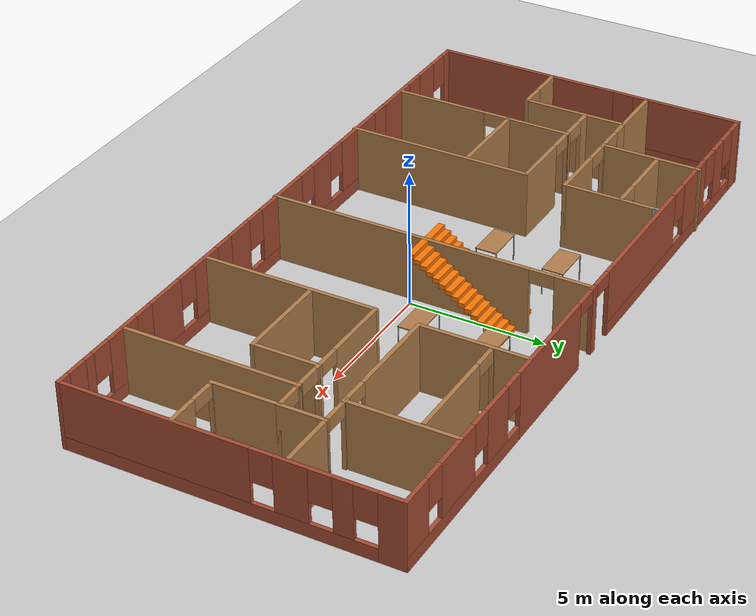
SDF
<sdf version="1.6">
 <world name="default">
  <plugin name="hello" filename="libhello.so"/>
  <model name="ground_plane">
   <static>1</static>
   <link name="link">
    <collision name="collision">
     <geometry><plane><normal>0 0 1</normal><size>100 100</size></plane></geometry>
     <surface><friction><ode><mu>100</mu><mu2>50</mu2></ode></friction></surface>
    </collision>
    <visual name="visual">
     <cast_shadows>0</cast_shadows>
     <geometry><plane><normal>0 0 1</normal><size>100 100</size></plane></geometry>
     <material>
      <script><uri>file://media/materials/scripts/gazebo.material</uri><name>Gazebo/Grey</name></script>
     </material>
    </visual>
   </link>
  </model>
  <gravity>0 0 -9.8</gravity>
  <magnetic_field>6e-06 2.3e-05 -4.2e-05</magnetic_field>
  <atmosphere type="adiabatic"/>
  <physics name="default_physics" default="0" type="ode">
   <max_step_size>0.001</max_step_size>
   <real_time_factor>1</real_time_factor>
   <real_time_update_rate>1000</real_time_update_rate>
  </physics>
  <scene><ambient>0.4 0.4 0.4 1</ambient><background>0.7 0.7 0.7 1</background><shadows>1</shadows></scene>
  <spherical_coordinates>
   <surface_model>EARTH_WGS84</surface_model>
   <latitude_deg>0</latitude_deg>
   <longitude_deg>0</longitude_deg>
   <elevation>0</elevation>
   <heading_deg>0</heading_deg>
  </spherical_coordinates>
  <model name="myhouse">
   <pose>-0.386417 0.578117 0 0 -0 0</pose>
   <link name="Stairs_1">
    <visual name="Stairs_1_Visual_0">
     <pose>0.612913 3.12759 0.083333 0 -0 0</pose>
     <geometry><box><size>1 0.233333 0.166667</size></box></geometry>
     <material>
      <script><uri>file://media/materials/scripts/gazebo.material</uri><name>Gazebo/Grey</name></script>
      <ambient>0.996078 0.47451 0.0196078 1</ambient>
     </material>
    </visual>
    <collision name="Stairs_1_Collision_0">
     <geometry><box><size>1 0.233333 0.166667</size></box></geometry>
     <pose>0.612913 3.12759 0.083333 0 -0 0</pose>
    </collision>
    <visual name="Stairs_1_Visual_1">
     <pose>0.612913 2.89426 0.25 0 -0 0</pose>
     <geometry><box><size>1 0.233333 0.166667</size></box></geometry>
     <material>
      <script><uri>file://media/materials/scripts/gazebo.material</uri><name>Gazebo/Grey</name></script>
      <ambient>0.996078 0.47451 0.0196078 1</ambient>
     </material>
    </visual>
    <collision name="Stairs_1_Collision_1">
     <geometry><box><size>1 0.233333 0.166667</size></box></geometry>
     <pose>0.612913 2.89426 0.25 0 -0 0</pose>
    </collision>
    <visual name="Stairs_1_Visual_2">
     <pose>0.612913 2.66093 0.416667 0 -0 0</pose>
     <geometry><box><size>1 0.233333 0.166667</size></box></geometry>
     <material>
      <script><uri>file://media/materials/scripts/gazebo.material</uri><name>Gazebo/Grey</name></script>
      <ambient>0.996078 0.47451 0.0196078 1</ambient>
     </material>
    </visual>
    <collision name="Stairs_1_Collision_2">
     <geometry><box><size>1 0.233333 0.166667</size></box></geometry>
     <pose>0.612913 2.66093 0.416667 0 -0 0</pose>
    </collision>
    <visual name="Stairs_1_Visual_3">
     <pose>0.612913 2.4276 0.583333 0 -0 0</pose>
     <geometry><box><size>1 0.233333 0.166667</size></box></geometry>
     <material>
      <script><uri>file://media/materials/scripts/gazebo.material</uri><name>Gazebo/Grey</name></script>
      <ambient>0.996078 0.47451 0.0196078 1</ambient>
     </material>
    </visual>
    <collision name="Stairs_1_Collision_3">
     <geometry><box><size>1 0.233333 0.166667</size></box></geometry>
     <pose>0.612913 2.4276 0.583333 0 -0 0</pose>
    </collision>
    <visual name="Stairs_1_Visual_4">
     <pose>0.612913 2.19426 0.75 0 -0 0</pose>
     <geometry><box><size>1 0.233333 0.166667</size></box></geometry>
     <material>
      <script><uri>file://media/materials/scripts/gazebo.material</uri><name>Gazebo/Grey</name></script>
      <ambient>0.996078 0.47451 0.0196078 1</ambient>
     </material>
    </visual>
    <collision name="Stairs_1_Collision_4">
     <geometry><box><size>1 0.233333 0.166667</size></box></geometry>
     <pose>0.612913 2.19426 0.75 0 -0 0</pose>
    </collision>
    <visual name="Stairs_1_Visual_5">
     <pose>0.612913 1.96093 0.916667 0 -0 0</pose>
     <geometry><box><size>1 0.233333 0.166667</size></box></geometry>
     <material>
      <script><uri>file://media/materials/scripts/gazebo.material</uri><name>Gazebo/Grey</name></script>
      <ambient>0.996078 0.47451 0.0196078 1</ambient>
     </material>
    </visual>
    <collision name="Stairs_1_Collision_5">
     <geometry><box><size>1 0.233333 0.166667</size></box></geometry>
     <pose>0.612913 1.96093 0.916667 0 -0 0</pose>
    </collision>
    <visual name="Stairs_1_Visual_6">
     <pose>0.612913 1.72759 1.08333 0 -0 0</pose>
     <geometry><box><size>1 0.233333 0.166667</size></box></geometry>
     <material>
      <script><uri>file://media/materials/scripts/gazebo.material</uri><name>Gazebo/Grey</name></script>
      <ambient>0.996078 0.47451 0.0196078 1</ambient>
     </material>
    </visual>
    <collision name="Stairs_1_Collision_6">
     <geometry><box><size>1 0.233333 0.166667</size></box></geometry>
     <pose>0.612913 1.72759 1.08333 0 -0 0</pose>
    </collision>
    <visual name="Stairs_1_Visual_7">
     <pose>0.612913 1.49426 1.25 0 -0 0</pose>
     <geometry><box><size>1 0.233333 0.166667</size></box></geometry>
     <material>
      <script><uri>file://media/materials/scripts/gazebo.material</uri><name>Gazebo/Grey</name></script>
      <ambient>0.996078 0.47451 0.0196078 1</ambient>
     </material>
    </visual>
    <collision name="Stairs_1_Collision_7">
     <geometry><box><size>1 0.233333 0.166667</size></box></geometry>
     <pose>0.612913 1.49426 1.25 0 -0 0</pose>
    </collision>
    <visual name="Stairs_1_Visual_8">
     <pose>0.612913 1.26093 1.41667 0 -0 0</pose>
     <geometry><box><size>1 0.233333 0.166667</size></box></geometry>
     <material>
      <script><uri>file://media/materials/scripts/gazebo.material</uri><name>Gazebo/Grey</name></script>
      <ambient>0.996078 0.47451 0.0196078 1</ambient>
     </material>
    </visual>
    <collision name="Stairs_1_Collision_8">
     <geometry><box><size>1 0.233333 0.166667</size></box></geometry>
     <pose>0.612913 1.26093 1.41667 0 -0 0</pose>
    </collision>
    <visual name="Stairs_1_Visual_9">
     <pose>0.612913 1.0276 1.58333 0 -0 0</pose>
     <geometry><box><size>1 0.233333 0.166667</size></box></geometry>
     <material>
      <script><uri>file://media/materials/scripts/gazebo.material</uri><name>Gazebo/Grey</name></script>
      <ambient>0.996078 0.47451 0.0196078 1</ambient>
     </material>
    </visual>
    <collision name="Stairs_1_Collision_9">
     <geometry><box><size>1 0.233333 0.166667</size></box></geometry>
     <pose>0.612913 1.0276 1.58333 0 -0 0</pose>
    </collision>
    <visual name="Stairs_1_Visual_10">
     <pose>0.612913 0.794262 1.75 0 -0 0</pose>
     <geometry><box><size>1 0.233333 0.166667</size></box></geometry>
     <material>
      <script><uri>file://media/materials/scripts/gazebo.material</uri><name>Gazebo/Grey</name></script>
      <ambient>0.996078 0.47451 0.0196078 1</ambient>
     </material>
    </visual>
    <collision name="Stairs_1_Collision_10">
     <geometry><box><size>1 0.233333 0.166667</size></box></geometry>
     <pose>0.612913 0.794262 1.75 0 -0 0</pose>
    </collision>
    <visual name="Stairs_1_Visual_11">
     <pose>0.612913 0.560929 1.91667 0 -0 0</pose>
     <geometry><box><size>1 0.233333 0.166667</size></box></geometry>
     <material>
      <script><uri>file://media/materials/scripts/gazebo.material</uri><name>Gazebo/Grey</name></script>
      <ambient>0.996078 0.47451 0.0196078 1</ambient>
     </material>
    </visual>
    <collision name="Stairs_1_Collision_11">
     <geometry><box><size>1 0.233333 0.166667</size></box></geometry>
     <pose>0.612913 0.560929 1.91667 0 -0 0</pose>
    </collision>
    <visual name="Stairs_1_Visual_12">
     <pose>0.612913 0.327595 2.08333 0 -0 0</pose>
     <geometry><box><size>1 0.233333 0.166667</size></box></geometry>
     <material>
      <script><uri>file://media/materials/scripts/gazebo.material</uri><name>Gazebo/Grey</name></script>
      <ambient>0.996078 0.47451 0.0196078 1</ambient>
     </material>
    </visual>
    <collision name="Stairs_1_Collision_12">
     <geometry><box><size>1 0.233333 0.166667</size></box></geometry>
     <pose>0.612913 0.327595 2.08333 0 -0 0</pose>
    </collision>
    <visual name="Stairs_1_Visual_13">
     <pose>0.612913 0.094262 2.25 0 -0 0</pose>
     <geometry><box><size>1 0.233333 0.166667</size></box></geometry>
     <material>
      <script><uri>file://media/materials/scripts/gazebo.material</uri><name>Gazebo/Grey</name></script>
      <ambient>0.996078 0.47451 0.0196078 1</ambient>
     </material>
    </visual>
    <collision name="Stairs_1_Collision_13">
     <geometry><box><size>1 0.233333 0.166667</size></box></geometry>
     <pose>0.612913 0.094262 2.25 0 -0 0</pose>
    </collision>
    <visual name="Stairs_1_Visual_14">
     <pose>0.612913 -0.139071 2.41667 0 -0 0</pose>
     <geometry><box><size>1 0.233333 0.166667</size></box></geometry>
     <material>
      <script><uri>file://media/materials/scripts/gazebo.material</uri><name>Gazebo/Grey</name></script>
      <ambient>0.996078 0.47451 0.0196078 1</ambient>
     </material>
    </visual>
    <collision name="Stairs_1_Collision_14">
     <geometry><box><size>1 0.233333 0.166667</size></box></geometry>
     <pose>0.612913 -0.139071 2.41667 0 -0 0</pose>
    </collision>
   </link>
   <link name="Stairs_2">
    <visual name="Stairs_2_Visual_0">
     <pose>-0.53356 3.12759 0.083333 0 -0 0</pose>
     <geometry><box><size>1 0.233333 0.166667</size></box></geometry>
     <material>
      <script><uri>file://media/materials/scripts/gazebo.material</uri><name>Gazebo/Grey</name></script>
      <ambient>0.996078 0.47451 0.0196078 1</ambient>
     </material>
    </visual>
    <collision name="Stairs_2_Collision_0">
     <geometry><box><size>1 0.233333 0.166667</size></box></geometry>
     <pose>-0.53356 3.12759 0.083333 0 -0 0</pose>
    </collision>
    <visual name="Stairs_2_Visual_1">
     <pose>-0.53356 2.89426 0.25 0 -0 0</pose>
     <geometry><box><size>1 0.233333 0.166667</size></box></geometry>
     <material>
      <script><uri>file://media/materials/scripts/gazebo.material</uri><name>Gazebo/Grey</name></script>
      <ambient>0.996078 0.47451 0.0196078 1</ambient>
     </material>
    </visual>
    <collision name="Stairs_2_Collision_1">
     <geometry><box><size>1 0.233333 0.166667</size></box></geometry>
     <pose>-0.53356 2.89426 0.25 0 -0 0</pose>
    </collision>
    <visual name="Stairs_2_Visual_2">
     <pose>-0.53356 2.66093 0.416667 0 -0 0</pose>
     <geometry><box><size>1 0.233333 0.166667</size></box></geometry>
     <material>
      <script><uri>file://media/materials/scripts/gazebo.material</uri><name>Gazebo/Grey</name></script>
      <ambient>0.996078 0.47451 0.0196078 1</ambient>
     </material>
    </visual>
    <collision name="Stairs_2_Collision_2">
     <geometry><box><size>1 0.233333 0.166667</size></box></geometry>
     <pose>-0.53356 2.66093 0.416667 0 -0 0</pose>
    </collision>
    <visual name="Stairs_2_Visual_3">
     <pose>-0.53356 2.4276 0.583333 0 -0 0</pose>
     <geometry><box><size>1 0.233333 0.166667</size></box></geometry>
     <material>
      <script><uri>file://media/materials/scripts/gazebo.material</uri><name>Gazebo/Grey</name></script>
      <ambient>0.996078 0.47451 0.0196078 1</ambient>
     </material>
    </visual>
    <collision name="Stairs_2_Collision_3">
     <geometry><box><size>1 0.233333 0.166667</size></box></geometry>
     <pose>-0.53356 2.4276 0.583333 0 -0 0</pose>
    </collision>
    <visual name="Stairs_2_Visual_4">
     <pose>-0.53356 2.19426 0.75 0 -0 0</pose>
     <geometry><box><size>1 0.233333 0.166667</size></box></geometry>
     <material>
      <script><uri>file://media/materials/scripts/gazebo.material</uri><name>Gazebo/Grey</name></script>
      <ambient>0.996078 0.47451 0.0196078 1</ambient>
     </material>
    </visual>
    <collision name="Stairs_2_Collision_4">
     <geometry><box><size>1 0.233333 0.166667</size></box></geometry>
     <pose>-0.53356 2.19426 0.75 0 -0 0</pose>
    </collision>
    <visual name="Stairs_2_Visual_5">
     <pose>-0.53356 1.96093 0.916667 0 -0 0</pose>
     <geometry><box><size>1 0.233333 0.166667</size></box></geometry>
     <material>
      <script><uri>file://media/materials/scripts/gazebo.material</uri><name>Gazebo/Grey</name></script>
      <ambient>0.996078 0.47451 0.0196078 1</ambient>
     </material>
    </visual>
    <collision name="Stairs_2_Collision_5">
     <geometry><box><size>1 0.233333 0.166667</size></box></geometry>
     <pose>-0.53356 1.96093 0.916667 0 -0 0</pose>
    </collision>
    <visual name="Stairs_2_Visual_6">
     <pose>-0.53356 1.72759 1.08333 0 -0 0</pose>
     <geometry><box><size>1 0.233333 0.166667</size></box></geometry>
     <material>
      <script><uri>file://media/materials/scripts/gazebo.material</uri><name>Gazebo/Grey</name></script>
      <ambient>0.996078 0.47451 0.0196078 1</ambient>
     </material>
    </visual>
    <collision name="Stairs_2_Collision_6">
     <geometry><box><size>1 0.233333 0.166667</size></box></geometry>
     <pose>-0.53356 1.72759 1.08333 0 -0 0</pose>
    </collision>
    <visual name="Stairs_2_Visual_7">
     <pose>-0.53356 1.49426 1.25 0 -0 0</pose>
     <geometry><box><size>1 0.233333 0.166667</size></box></geometry>
     <material>
      <script><uri>file://media/materials/scripts/gazebo.material</uri><name>Gazebo/Grey</name></script>
      <ambient>0.996078 0.47451 0.0196078 1</ambient>
     </material>
    </visual>
    <collision name="Stairs_2_Collision_7">
     <geometry><box><size>1 0.233333 0.166667</size></box></geometry>
     <pose>-0.53356 1.49426 1.25 0 -0 0</pose>
    </collision>
    <visual name="Stairs_2_Visual_8">
     <pose>-0.53356 1.26093 1.41667 0 -0 0</pose>
     <geometry><box><size>1 0.233333 0.166667</size></box></geometry>
     <material>
      <script><uri>file://media/materials/scripts/gazebo.material</uri><name>Gazebo/Grey</name></script>
      <ambient>0.996078 0.47451 0.0196078 1</ambient>
     </material>
    </visual>
    <collision name="Stairs_2_Collision_8">
     <geometry><box><size>1 0.233333 0.166667</size></box></geometry>
     <pose>-0.53356 1.26093 1.41667 0 -0 0</pose>
    </collision>
    <visual name="Stairs_2_Visual_9">
     <pose>-0.53356 1.0276 1.58333 0 -0 0</pose>
     <geometry><box><size>1 0.233333 0.166667</size></box></geometry>
     <material>
      <script><uri>file://media/materials/scripts/gazebo.material</uri><name>Gazebo/Grey</name></script>
      <ambient>0.996078 0.47451 0.0196078 1</ambient>
     </material>
    </visual>
    <collision name="Stairs_2_Collision_9">
     <geometry><box><size>1 0.233333 0.166667</size></box></geometry>
     <pose>-0.53356 1.0276 1.58333 0 -0 0</pose>
    </collision>
    <visual name="Stairs_2_Visual_10">
     <pose>-0.53356 0.794262 1.75 0 -0 0</pose>
     <geometry><box><size>1 0.233333 0.166667</size></box></geometry>
     <material>
      <script><uri>file://media/materials/scripts/gazebo.material</uri><name>Gazebo/Grey</name></script>
      <ambient>0.996078 0.47451 0.0196078 1</ambient>
     </material>
    </visual>
    <collision name="Stairs_2_Collision_10">
     <geometry><box><size>1 0.233333 0.166667</size></box></geometry>
     <pose>-0.53356 0.794262 1.75 0 -0 0</pose>
    </collision>
    <visual name="Stairs_2_Visual_11">
     <pose>-0.53356 0.560929 1.91667 0 -0 0</pose>
     <geometry><box><size>1 0.233333 0.166667</size></box></geometry>
     <material>
      <script><uri>file://media/materials/scripts/gazebo.material</uri><name>Gazebo/Grey</name></script>
      <ambient>0.996078 0.47451 0.0196078 1</ambient>
     </material>
    </visual>
    <collision name="Stairs_2_Collision_11">
     <geometry><box><size>1 0.233333 0.166667</size></box></geometry>
     <pose>-0.53356 0.560929 1.91667 0 -0 0</pose>
    </collision>
    <visual name="Stairs_2_Visual_12">
     <pose>-0.53356 0.327595 2.08333 0 -0 0</pose>
     <geometry><box><size>1 0.233333 0.166667</size></box></geometry>
     <material>
      <script><uri>file://media/materials/scripts/gazebo.material</uri><name>Gazebo/Grey</name></script>
      <ambient>0.996078 0.47451 0.0196078 1</ambient>
     </material>
    </visual>
    <collision name="Stairs_2_Collision_12">
     <geometry><box><size>1 0.233333 0.166667</size></box></geometry>
     <pose>-0.53356 0.327595 2.08333 0 -0 0</pose>
    </collision>
    <visual name="Stairs_2_Visual_13">
     <pose>-0.53356 0.094262 2.25 0 -0 0</pose>
     <geometry><box><size>1 0.233333 0.166667</size></box></geometry>
     <material>
      <script><uri>file://media/materials/scripts/gazebo.material</uri><name>Gazebo/Grey</name></script>
      <ambient>0.996078 0.47451 0.0196078 1</ambient>
     </material>
    </visual>
    <collision name="Stairs_2_Collision_13">
     <geometry><box><size>1 0.233333 0.166667</size></box></geometry>
     <pose>-0.53356 0.094262 2.25 0 -0 0</pose>
    </collision>
    <visual name="Stairs_2_Visual_14">
     <pose>-0.53356 -0.139071 2.41667 0 -0 0</pose>
     <geometry><box><size>1 0.233333 0.166667</size></box></geometry>
     <material>
      <script><uri>file://media/materials/scripts/gazebo.material</uri><name>Gazebo/Grey</name></script>
      <ambient>0.996078 0.47451 0.0196078 1</ambient>
     </material>
    </visual>
    <collision name="Stairs_2_Collision_14">
     <geometry><box><size>1 0.233333 0.166667</size></box></geometry>
     <pose>-0.53356 -0.139071 2.41667 0 -0 0</pose>
    </collision>
   </link>
   <link name="Wall_10">
    <pose>-12.3 -0.005752 0 0 -0 1.5708</pose>
    <visual name="Wall_10_Visual_0">
     <pose>-2.48016 0 1.25 0 -0 0</pose>
     <geometry><box><size>7.03967 0.15 2.5</size></box></geometry>
     <material>
      <script><uri>file://media/materials/scripts/gazebo.material</uri><name>Gazebo/Bricks</name></script>
      <ambient>0.435294 0.796078 0.67451 1</ambient>
     </material>
    </visual>
    <collision name="Wall_10_Collision_0">
     <geometry><box><size>7.03967 0.15 2.5</size></box></geometry>
     <pose>-2.48016 0 1.25 0 -0 0</pose>
    </collision>
    <visual name="Wall_10_Visual_1">
     <pose>3.51984 0 0.25 0 -0 0</pose>
     <geometry><box><size>4.96033 0.15 0.5</size></box></geometry>
     <material>
      <script><uri>file://media/materials/scripts/gazebo.material</uri><name>Gazebo/Bricks</name></script>
      <ambient>0.435294 0.796078 0.67451 1</ambient>
     </material>
    </visual>
    <collision name="Wall_10_Collision_1">
     <geometry><box><size>4.96033 0.15 0.5</size></box></geometry>
     <pose>3.51984 0 0.25 0 -0 0</pose>
    </collision>
    <visual name="Wall_10_Visual_2">
     <pose>3.91984 0 1.5 0 -0 0</pose>
     <geometry><box><size>4.16033 0.15 2</size></box></geometry>
     <material>
      <script><uri>file://media/materials/scripts/gazebo.material</uri><name>Gazebo/Bricks</name></script>
      <ambient>0.435294 0.796078 0.67451 1</ambient>
     </material>
    </visual>
    <collision name="Wall_10_Collision_2">
     <geometry><box><size>4.16033 0.15 2</size></box></geometry>
     <pose>3.91984 0 1.5 0 -0 0</pose>
    </collision>
    <visual name="Wall_10_Visual_3">
     <pose>1.43967 0 1.9 0 -0 0</pose>
     <geometry><box><size>0.8 0.15 1.2</size></box></geometry>
     <material>
      <script><uri>file://media/materials/scripts/gazebo.material</uri><name>Gazebo/Bricks</name></script>
      <ambient>0.435294 0.796078 0.67451 1</ambient>
     </material>
    </visual>
    <collision name="Wall_10_Collision_3">
     <geometry><box><size>0.8 0.15 1.2</size></box></geometry>
     <pose>1.43967 0 1.9 0 -0 0</pose>
    </collision>
   </link>
   <link name="Wall_14">
    <collision name="Wall_14_Collision">
     <geometry><box><size>0.16 0.15 2.5</size></box></geometry>
     <pose>0 0 1.25 0 -0 0</pose>
    </collision>
    <visual name="Wall_14_Visual">
     <pose>0 0 1.25 0 -0 0</pose>
     <geometry><box><size>0.16 0.15 2.5</size></box></geometry>
     <material>
      <script><uri>file://media/materials/scripts/gazebo.material</uri><name>Gazebo/Grey</name></script>
      <ambient>1 1 1 1</ambient>
     </material>
    </visual>
    <pose>0.03462 5.87902 0 0 -0 0</pose>
   </link>
   <link name="Wall_15">
    <pose>0.03962 -0.045979 0 0 0 -1.5708</pose>
    <visual name="Wall_15_Visual_0">
     <pose>-5.3025 0 1.25 0 -0 0</pose>
     <geometry><box><size>1.39499 0.15 2.5</size></box></geometry>
     <material>
      <script><uri>file://media/materials/scripts/gazebo.material</uri><name>Gazebo/Wood</name></script>
      <ambient>1 1 1 1</ambient>
     </material>
    </visual>
    <collision name="Wall_15_Collision_0">
     <geometry><box><size>1.39499 0.15 2.5</size></box></geometry>
     <pose>-5.3025 0 1.25 0 -0 0</pose>
    </collision>
    <visual name="Wall_15_Visual_1">
     <pose>1.1475 0 1.25 0 -0 0</pose>
     <geometry><box><size>9.70501 0.15 2.5</size></box></geometry>
     <material>
      <script><uri>file://media/materials/scripts/gazebo.material</uri><name>Gazebo/Wood</name></script>
      <ambient>1 1 1 1</ambient>
     </material>
    </visual>
    <collision name="Wall_15_Collision_1">
     <geometry><box><size>9.70501 0.15 2.5</size></box></geometry>
     <pose>1.1475 0 1.25 0 -0 0</pose>
    </collision>
    <visual name="Wall_15_Visual_2">
     <pose>-4.15501 0 2.25 0 -0 0</pose>
     <geometry><box><size>0.9 0.15 0.5</size></box></geometry>
     <material>
      <script><uri>file://media/materials/scripts/gazebo.material</uri><name>Gazebo/Wood</name></script>
      <ambient>1 1 1 1</ambient>
     </material>
    </visual>
    <collision name="Wall_15_Collision_2">
     <geometry><box><size>0.9 0.15 0.5</size></box></geometry>
     <pose>-4.15501 0 2.25 0 -0 0</pose>
    </collision>
   </link>
   <link name="Wall_17">
    <collision name="Wall_17_Collision">
     <geometry><box><size>6.5 0.15 2.5</size></box></geometry>
     <pose>0 0 1.25 0 -0 0</pose>
    </collision>
    <visual name="Wall_17_Visual">
     <pose>0 0 1.25 0 -0 0</pose>
     <geometry><box><size>6.5 0.15 2.5</size></box></geometry>
     <material>
      <script><uri>file://media/materials/scripts/gazebo.material</uri><name>Gazebo/Wood</name></script>
      <ambient>1 1 1 1</ambient>
     </material>
    </visual>
    <pose>4.43449 -2.73253 0 0 -0 1.5708</pose>
   </link>
   <link name="Wall_18">
    <pose>6.73449 0.442468 0 0 -0 0</pose>
    <visual name="Wall_18_Visual_0">
     <pose>-1.08415 0 1.25 0 -0 0</pose>
     <geometry><box><size>2.58169 0.15 2.5</size></box></geometry>
     <material>
      <script><uri>file://media/materials/scripts/gazebo.material</uri><name>Gazebo/Wood</name></script>
      <ambient>1 1 1 1</ambient>
     </material>
    </visual>
    <collision name="Wall_18_Collision_0">
     <geometry><box><size>2.58169 0.15 2.5</size></box></geometry>
     <pose>-1.08415 0 1.25 0 -0 0</pose>
    </collision>
    <visual name="Wall_18_Visual_1">
     <pose>1.20982 0 1.25 0 -0 0</pose>
     <geometry><box><size>0.206246 0.15 2.5</size></box></geometry>
     <material>
      <script><uri>file://media/materials/scripts/gazebo.material</uri><name>Gazebo/Wood</name></script>
      <ambient>1 1 1 1</ambient>
     </material>
    </visual>
    <collision name="Wall_18_Collision_1">
     <geometry><box><size>0.206246 0.15 2.5</size></box></geometry>
     <pose>1.20982 0 1.25 0 -0 0</pose>
    </collision>
    <visual name="Wall_18_Visual_2">
     <pose>2.29397 0 1.25 0 -0 0</pose>
     <geometry><box><size>0.162059 0.15 2.5</size></box></geometry>
     <material>
      <script><uri>file://media/materials/scripts/gazebo.material</uri><name>Gazebo/Wood</name></script>
      <ambient>1 1 1 1</ambient>
     </material>
    </visual>
    <collision name="Wall_18_Collision_2">
     <geometry><box><size>0.162059 0.15 2.5</size></box></geometry>
     <pose>2.29397 0 1.25 0 -0 0</pose>
    </collision>
    <visual name="Wall_18_Visual_3">
     <pose>0.656695 0 2.25 0 -0 0</pose>
     <geometry><box><size>0.9 0.15 0.5</size></box></geometry>
     <material>
      <script><uri>file://media/materials/scripts/gazebo.material</uri><name>Gazebo/Wood</name></script>
      <ambient>1 1 1 1</ambient>
     </material>
    </visual>
    <collision name="Wall_18_Collision_3">
     <geometry><box><size>0.9 0.15 0.5</size></box></geometry>
     <pose>0.656695 0 2.25 0 -0 0</pose>
    </collision>
    <visual name="Wall_18_Visual_4">
     <pose>1.76294 0 2.25 0 -0 0</pose>
     <geometry><box><size>0.9 0.15 0.5</size></box></geometry>
     <material>
      <script><uri>file://media/materials/scripts/gazebo.material</uri><name>Gazebo/Wood</name></script>
      <ambient>1 1 1 1</ambient>
     </material>
    </visual>
    <collision name="Wall_18_Collision_4">
     <geometry><box><size>0.9 0.15 0.5</size></box></geometry>
     <pose>1.76294 0 2.25 0 -0 0</pose>
    </collision>
   </link>
   <link name="Wall_19">
    <collision name="Wall_19_Collision">
     <geometry><box><size>6.5 0.15 2.5</size></box></geometry>
     <pose>0 0 1.25 0 -0 0</pose>
    </collision>
    <visual name="Wall_19_Visual">
     <pose>0 0 1.25 0 -0 0</pose>
     <geometry><box><size>6.5 0.15 2.5</size></box></geometry>
     <material>
      <script><uri>file://media/materials/scripts/gazebo.material</uri><name>Gazebo/Wood</name></script>
      <ambient>1 1 1 1</ambient>
     </material>
    </visual>
    <pose>9.03449 -2.73253 0 0 0 -1.5708</pose>
   </link>
   <link name="Wall_21">
    <collision name="Wall_21_Collision">
     <geometry><box><size>2.5 0.15 2.5</size></box></geometry>
     <pose>0 0 1.25 0 -0 0</pose>
    </collision>
    <visual name="Wall_21_Visual">
     <pose>0 0 1.25 0 -0 0</pose>
     <geometry><box><size>2.5 0.15 2.5</size></box></geometry>
     <material>
      <script><uri>file://media/materials/scripts/gazebo.material</uri><name>Gazebo/Wood</name></script>
      <ambient>1 1 1 1</ambient>
     </material>
    </visual>
    <pose>7.87391 -0.726644 0 0 0 -1.5708</pose>
   </link>
   <link name="Wall_22">
    <collision name="Wall_22_Collision">
     <geometry><box><size>3.5 0.15 2.5</size></box></geometry>
     <pose>0 0 1.25 0 -0 0</pose>
    </collision>
    <visual name="Wall_22_Visual">
     <pose>0 0 1.25 0 -0 0</pose>
     <geometry><box><size>3.5 0.15 2.5</size></box></geometry>
     <material>
      <script><uri>file://media/materials/scripts/gazebo.material</uri><name>Gazebo/Wood</name></script>
      <ambient>1 1 1 1</ambient>
     </material>
    </visual>
    <pose>6.19891 -1.90164 0 0 -0 3.14159</pose>
   </link>
   <link name="Wall_24">
    <pose>9.58449 0.442468 0 0 -0 0</pose>
    <visual name="Wall_24_Visual_0">
     <pose>-0.51785 0 1.25 0 -0 0</pose>
     <geometry><box><size>0.214301 0.15 2.5</size></box></geometry>
     <material>
      <script><uri>file://media/materials/scripts/gazebo.material</uri><name>Gazebo/Wood</name></script>
      <ambient>1 1 1 1</ambient>
     </material>
    </visual>
    <collision name="Wall_24_Collision_0">
     <geometry><box><size>0.214301 0.15 2.5</size></box></geometry>
     <pose>-0.51785 0 1.25 0 -0 0</pose>
    </collision>
    <visual name="Wall_24_Visual_1">
     <pose>0.55715 0 1.25 0 -0 0</pose>
     <geometry><box><size>0.135699 0.15 2.5</size></box></geometry>
     <material>
      <script><uri>file://media/materials/scripts/gazebo.material</uri><name>Gazebo/Wood</name></script>
      <ambient>1 1 1 1</ambient>
     </material>
    </visual>
    <collision name="Wall_24_Collision_1">
     <geometry><box><size>0.135699 0.15 2.5</size></box></geometry>
     <pose>0.55715 0 1.25 0 -0 0</pose>
    </collision>
    <visual name="Wall_24_Visual_2">
     <pose>0.039301 0 2.25 0 -0 0</pose>
     <geometry><box><size>0.9 0.15 0.5</size></box></geometry>
     <material>
      <script><uri>file://media/materials/scripts/gazebo.material</uri><name>Gazebo/Wood</name></script>
      <ambient>1 1 1 1</ambient>
     </material>
    </visual>
    <collision name="Wall_24_Collision_2">
     <geometry><box><size>0.9 0.15 0.5</size></box></geometry>
     <pose>0.039301 0 2.25 0 -0 0</pose>
    </collision>
   </link>
   <link name="Wall_25">
    <collision name="Wall_25_Collision">
     <geometry><box><size>1.75 0.15 2.5</size></box></geometry>
     <pose>0 0 1.25 0 -0 0</pose>
    </collision>
    <visual name="Wall_25_Visual">
     <pose>0 0 1.25 0 -0 0</pose>
     <geometry><box><size>1.75 0.15 2.5</size></box></geometry>
     <material>
      <script><uri>file://media/materials/scripts/gazebo.material</uri><name>Gazebo/Wood</name></script>
      <ambient>1 1 1 1</ambient>
     </material>
    </visual>
    <pose>10.1345 1.24247 0 0 -0 1.5708</pose>
   </link>
   <link name="Wall_26">
    <collision name="Wall_26_Collision">
     <geometry><box><size>2.25 0.15 2.5</size></box></geometry>
     <pose>0 0 1.25 0 -0 0</pose>
    </collision>
    <visual name="Wall_26_Visual">
     <pose>0 0 1.25 0 -0 0</pose>
     <geometry><box><size>2.25 0.15 2.5</size></box></geometry>
     <material>
      <script><uri>file://media/materials/scripts/gazebo.material</uri><name>Gazebo/Wood</name></script>
      <ambient>1 1 1 1</ambient>
     </material>
    </visual>
    <pose>11.1845 2.04247 0 0 -0 0</pose>
   </link>
   <link name="Wall_28">
    <collision name="Wall_28_Collision">
     <geometry><box><size>2.5 0.15 2.5</size></box></geometry>
     <pose>0 0 1.25 0 -0 0</pose>
    </collision>
    <visual name="Wall_28_Visual">
     <pose>0 0 1.25 0 -0 0</pose>
     <geometry><box><size>2.5 0.15 2.5</size></box></geometry>
     <material>
      <script><uri>file://media/materials/scripts/gazebo.material</uri><name>Gazebo/Wood</name></script>
      <ambient>1 1 1 1</ambient>
     </material>
    </visual>
    <pose>10.1345 -0.732532 0 0 0 -1.5708</pose>
   </link>
   <link name="Wall_29">
    <pose>11.1845 -1.90753 0 0 -0 0</pose>
    <visual name="Wall_29_Visual_0">
     <pose>-1.02478 0 1.25 0 -0 0</pose>
     <geometry><box><size>0.200434 0.15 2.5</size></box></geometry>
     <material>
      <script><uri>file://media/materials/scripts/gazebo.material</uri><name>Gazebo/Wood</name></script>
      <ambient>1 1 1 1</ambient>
     </material>
    </visual>
    <collision name="Wall_29_Collision_0">
     <geometry><box><size>0.200434 0.15 2.5</size></box></geometry>
     <pose>-1.02478 0 1.25 0 -0 0</pose>
    </collision>
    <visual name="Wall_29_Visual_1">
     <pose>0.550217 0 1.25 0 -0 0</pose>
     <geometry><box><size>1.14957 0.15 2.5</size></box></geometry>
     <material>
      <script><uri>file://media/materials/scripts/gazebo.material</uri><name>Gazebo/Wood</name></script>
      <ambient>1 1 1 1</ambient>
     </material>
    </visual>
    <collision name="Wall_29_Collision_1">
     <geometry><box><size>1.14957 0.15 2.5</size></box></geometry>
     <pose>0.550217 0 1.25 0 -0 0</pose>
    </collision>
    <visual name="Wall_29_Visual_2">
     <pose>-0.474566 0 2.25 0 -0 0</pose>
     <geometry><box><size>0.9 0.15 0.5</size></box></geometry>
     <material>
      <script><uri>file://media/materials/scripts/gazebo.material</uri><name>Gazebo/Wood</name></script>
      <ambient>1 1 1 1</ambient>
     </material>
    </visual>
    <collision name="Wall_29_Collision_2">
     <geometry><box><size>0.9 0.15 0.5</size></box></geometry>
     <pose>-0.474566 0 2.25 0 -0 0</pose>
    </collision>
   </link>
   <link name="Wall_31">
    <pose>7.33449 2.04247 0 0 -0 3.14159</pose>
    <visual name="Wall_31_Visual_0">
     <pose>-2.80715 0 1.25 0 -0 0</pose>
     <geometry><box><size>0.135699 0.15 2.5</size></box></geometry>
     <material>
      <script><uri>file://media/materials/scripts/gazebo.material</uri><name>Gazebo/Wood</name></script>
      <ambient>1 1 1 1</ambient>
     </material>
    </visual>
    <collision name="Wall_31_Collision_0">
     <geometry><box><size>0.135699 0.15 2.5</size></box></geometry>
     <pose>-2.80715 0 1.25 0 -0 0</pose>
    </collision>
    <visual name="Wall_31_Visual_1">
     <pose>-1.69595 0 1.25 0 -0 0</pose>
     <geometry><box><size>0.286701 0.15 2.5</size></box></geometry>
     <material>
      <script><uri>file://media/materials/scripts/gazebo.material</uri><name>Gazebo/Wood</name></script>
      <ambient>1 1 1 1</ambient>
     </material>
    </visual>
    <collision name="Wall_31_Collision_1">
     <geometry><box><size>0.286701 0.15 2.5</size></box></geometry>
     <pose>-1.69595 0 1.25 0 -0 0</pose>
    </collision>
    <visual name="Wall_31_Visual_2">
     <pose>1.1112 0 1.25 0 -0 0</pose>
     <geometry><box><size>3.5276 0.15 2.5</size></box></geometry>
     <material>
      <script><uri>file://media/materials/scripts/gazebo.material</uri><name>Gazebo/Wood</name></script>
      <ambient>1 1 1 1</ambient>
     </material>
    </visual>
    <collision name="Wall_31_Collision_2">
     <geometry><box><size>3.5276 0.15 2.5</size></box></geometry>
     <pose>1.1112 0 1.25 0 -0 0</pose>
    </collision>
    <visual name="Wall_31_Visual_3">
     <pose>-2.2893 0 2.25 0 -0 0</pose>
     <geometry><box><size>0.9 0.15 0.5</size></box></geometry>
     <material>
      <script><uri>file://media/materials/scripts/gazebo.material</uri><name>Gazebo/Wood</name></script>
      <ambient>1 1 1 1</ambient>
     </material>
    </visual>
    <collision name="Wall_31_Collision_3">
     <geometry><box><size>0.9 0.15 0.5</size></box></geometry>
     <pose>-2.2893 0 2.25 0 -0 0</pose>
    </collision>
    <visual name="Wall_31_Visual_4">
     <pose>-1.1026 0 2.25 0 -0 0</pose>
     <geometry><box><size>0.9 0.15 0.5</size></box></geometry>
     <material>
      <script><uri>file://media/materials/scripts/gazebo.material</uri><name>Gazebo/Wood</name></script>
      <ambient>1 1 1 1</ambient>
     </material>
    </visual>
    <collision name="Wall_31_Collision_4">
     <geometry><box><size>0.9 0.15 0.5</size></box></geometry>
     <pose>-1.1026 0 2.25 0 -0 0</pose>
    </collision>
   </link>
   <link name="Wall_32">
    <collision name="Wall_32_Collision">
     <geometry><box><size>4 0.15 2.5</size></box></geometry>
     <pose>0 0 1.25 0 -0 0</pose>
    </collision>
    <visual name="Wall_32_Visual">
     <pose>0 0 1.25 0 -0 0</pose>
     <geometry><box><size>4 0.15 2.5</size></box></geometry>
     <material>
      <script><uri>file://media/materials/scripts/gazebo.material</uri><name>Gazebo/Wood</name></script>
      <ambient>1 1 1 1</ambient>
     </material>
    </visual>
    <pose>4.53449 3.96747 0 0 -0 1.5708</pose>
   </link>
   <link name="Wall_34">
    <collision name="Wall_34_Collision">
     <geometry><box><size>0.16 0.15 2.5</size></box></geometry>
     <pose>0 0 1.25 0 -0 0</pose>
    </collision>
    <visual name="Wall_34_Visual">
     <pose>0 0 1.25 0 -0 0</pose>
     <geometry><box><size>0.16 0.15 2.5</size></box></geometry>
     <material>
      <script><uri>file://media/materials/scripts/gazebo.material</uri><name>Gazebo/Grey</name></script>
      <ambient>1 1 1 1</ambient>
     </material>
    </visual>
    <pose>9.0455 2.05744 0 0 -0 0</pose>
   </link>
   <link name="Wall_35">
    <collision name="Wall_35_Collision">
     <geometry><box><size>4 0.15 2.5</size></box></geometry>
     <pose>0 0 1.25 0 -0 0</pose>
    </collision>
    <visual name="Wall_35_Visual">
     <pose>0 0 1.25 0 -0 0</pose>
     <geometry><box><size>4 0.15 2.5</size></box></geometry>
     <material>
      <script><uri>file://media/materials/scripts/gazebo.material</uri><name>Gazebo/Wood</name></script>
      <ambient>1 1 1 1</ambient>
     </material>
    </visual>
    <pose>9.0505 3.98244 0 0 -0 1.5708</pose>
   </link>
   <link name="Wall_37">
    <pose>6.71006 4.63198 0 0 -0 0</pose>
    <visual name="Wall_37_Visual_0">
     <pose>-2.15591 0 1.25 0 -0 0</pose>
     <geometry><box><size>0.18818 0.15 2.5</size></box></geometry>
     <material>
      <script><uri>file://media/materials/scripts/gazebo.material</uri><name>Gazebo/Wood</name></script>
      <ambient>1 1 1 1</ambient>
     </material>
    </visual>
    <collision name="Wall_37_Collision_0">
     <geometry><box><size>0.18818 0.15 2.5</size></box></geometry>
     <pose>-2.15591 0 1.25 0 -0 0</pose>
    </collision>
    <visual name="Wall_37_Visual_1">
     <pose>0.54409 0 1.25 0 -0 0</pose>
     <geometry><box><size>3.41182 0.15 2.5</size></box></geometry>
     <material>
      <script><uri>file://media/materials/scripts/gazebo.material</uri><name>Gazebo/Wood</name></script>
      <ambient>1 1 1 1</ambient>
     </material>
    </visual>
    <collision name="Wall_37_Collision_1">
     <geometry><box><size>3.41182 0.15 2.5</size></box></geometry>
     <pose>0.54409 0 1.25 0 -0 0</pose>
    </collision>
    <visual name="Wall_37_Visual_2">
     <pose>-1.61182 0 2.25 0 -0 0</pose>
     <geometry><box><size>0.9 0.15 0.5</size></box></geometry>
     <material>
      <script><uri>file://media/materials/scripts/gazebo.material</uri><name>Gazebo/Wood</name></script>
      <ambient>1 1 1 1</ambient>
     </material>
    </visual>
    <collision name="Wall_37_Collision_2">
     <geometry><box><size>0.9 0.15 0.5</size></box></geometry>
     <pose>-1.61182 0 2.25 0 -0 0</pose>
    </collision>
   </link>
   <link name="Wall_40">
    <collision name="Wall_40_Collision">
     <geometry><box><size>2.25 0.15 2.5</size></box></geometry>
     <pose>0 0 1.25 0 -0 0</pose>
    </collision>
    <visual name="Wall_40_Visual">
     <pose>0 0 1.25 0 -0 0</pose>
     <geometry><box><size>2.25 0.15 2.5</size></box></geometry>
     <material>
      <script><uri>file://media/materials/scripts/gazebo.material</uri><name>Gazebo/Wood</name></script>
      <ambient>1 1 1 1</ambient>
     </material>
    </visual>
    <pose>-11.2299 2.35915 0 0 -0 0</pose>
   </link>
   <link name="Wall_41">
    <collision name="Wall_41_Collision">
     <geometry><box><size>4 0.15 2.5</size></box></geometry>
     <pose>0 0 1.25 0 -0 0</pose>
    </collision>
    <visual name="Wall_41_Visual">
     <pose>0 0 1.25 0 -0 0</pose>
     <geometry><box><size>4 0.15 2.5</size></box></geometry>
     <material>
      <script><uri>file://media/materials/scripts/gazebo.material</uri><name>Gazebo/Wood</name></script>
      <ambient>1 1 1 1</ambient>
     </material>
    </visual>
    <pose>-10.1799 0.434146 0 0 0 -1.5708</pose>
   </link>
   <link name="Wall_42">
    <pose>-11.2299 -1.49085 0 0 -0 3.14159</pose>
    <visual name="Wall_42_Visual_0">
     <pose>-1.0771 0 1.25 0 -0 0</pose>
     <geometry><box><size>0.0958 0.15 2.5</size></box></geometry>
     <material>
      <script><uri>file://media/materials/scripts/gazebo.material</uri><name>Gazebo/Wood</name></script>
      <ambient>1 1 1 1</ambient>
     </material>
    </visual>
    <collision name="Wall_42_Collision_0">
     <geometry><box><size>0.0958 0.15 2.5</size></box></geometry>
     <pose>-1.0771 0 1.25 0 -0 0</pose>
    </collision>
    <visual name="Wall_42_Visual_1">
     <pose>0.4979 0 1.25 0 -0 0</pose>
     <geometry><box><size>1.2542 0.15 2.5</size></box></geometry>
     <material>
      <script><uri>file://media/materials/scripts/gazebo.material</uri><name>Gazebo/Wood</name></script>
      <ambient>1 1 1 1</ambient>
     </material>
    </visual>
    <collision name="Wall_42_Collision_1">
     <geometry><box><size>1.2542 0.15 2.5</size></box></geometry>
     <pose>0.4979 0 1.25 0 -0 0</pose>
    </collision>
    <visual name="Wall_42_Visual_2">
     <pose>-0.5792 0 2.25 0 -0 0</pose>
     <geometry><box><size>0.9 0.15 0.5</size></box></geometry>
     <material>
      <script><uri>file://media/materials/scripts/gazebo.material</uri><name>Gazebo/Wood</name></script>
      <ambient>1 1 1 1</ambient>
     </material>
    </visual>
    <collision name="Wall_42_Collision_2">
     <geometry><box><size>0.9 0.15 0.5</size></box></geometry>
     <pose>-0.5792 0 2.25 0 -0 0</pose>
    </collision>
   </link>
   <link name="Wall_44">
    <pose>-7.75489 2.35915 0 0 -0 0</pose>
    <visual name="Wall_44_Visual_0">
     <pose>-2.11836 0 1.25 0 -0 0</pose>
     <geometry><box><size>0.763284 0.15 2.5</size></box></geometry>
     <material>
      <script><uri>file://media/materials/scripts/gazebo.material</uri><name>Gazebo/Wood</name></script>
      <ambient>1 1 1 1</ambient>
     </material>
    </visual>
    <collision name="Wall_44_Collision_0">
     <geometry><box><size>0.763284 0.15 2.5</size></box></geometry>
     <pose>-2.11836 0 1.25 0 -0 0</pose>
    </collision>
    <visual name="Wall_44_Visual_1">
     <pose>-0.703422 0 1.25 0 -0 0</pose>
     <geometry><box><size>0.266588 0.15 2.5</size></box></geometry>
     <material>
      <script><uri>file://media/materials/scripts/gazebo.material</uri><name>Gazebo/Wood</name></script>
      <ambient>1 1 1 1</ambient>
     </material>
    </visual>
    <collision name="Wall_44_Collision_1">
     <geometry><box><size>0.266588 0.15 2.5</size></box></geometry>
     <pose>-0.703422 0 1.25 0 -0 0</pose>
    </collision>
    <visual name="Wall_44_Visual_2">
     <pose>1.41494 0 1.25 0 -0 0</pose>
     <geometry><box><size>2.17013 0.15 2.5</size></box></geometry>
     <material>
      <script><uri>file://media/materials/scripts/gazebo.material</uri><name>Gazebo/Wood</name></script>
      <ambient>1 1 1 1</ambient>
     </material>
    </visual>
    <collision name="Wall_44_Collision_2">
     <geometry><box><size>2.17013 0.15 2.5</size></box></geometry>
     <pose>1.41494 0 1.25 0 -0 0</pose>
    </collision>
    <visual name="Wall_44_Visual_3">
     <pose>-1.28672 0 2.25 0 -0 0</pose>
     <geometry><box><size>0.9 0.15 0.5</size></box></geometry>
     <material>
      <script><uri>file://media/materials/scripts/gazebo.material</uri><name>Gazebo/Wood</name></script>
      <ambient>1 1 1 1</ambient>
     </material>
    </visual>
    <collision name="Wall_44_Collision_3">
     <geometry><box><size>0.9 0.15 0.5</size></box></geometry>
     <pose>-1.28672 0 2.25 0 -0 0</pose>
    </collision>
    <visual name="Wall_44_Visual_4">
     <pose>-0.120128 0 2.25 0 -0 0</pose>
     <geometry><box><size>0.9 0.15 0.5</size></box></geometry>
     <material>
      <script><uri>file://media/materials/scripts/gazebo.material</uri><name>Gazebo/Wood</name></script>
      <ambient>1 1 1 1</ambient>
     </material>
    </visual>
    <collision name="Wall_44_Collision_4">
     <geometry><box><size>0.9 0.15 0.5</size></box></geometry>
     <pose>-0.120128 0 2.25 0 -0 0</pose>
    </collision>
   </link>
   <link name="Wall_45">
    <collision name="Wall_45_Collision">
     <geometry><box><size>3.5 0.15 2.5</size></box></geometry>
     <pose>0 0 1.25 0 -0 0</pose>
    </collision>
    <visual name="Wall_45_Visual">
     <pose>0 0 1.25 0 -0 0</pose>
     <geometry><box><size>3.5 0.15 2.5</size></box></geometry>
     <material>
      <script><uri>file://media/materials/scripts/gazebo.material</uri><name>Gazebo/Wood</name></script>
      <ambient>1 1 1 1</ambient>
     </material>
    </visual>
    <pose>-5.32989 4.03414 0 0 -0 1.5708</pose>
   </link>
   <link name="Wall_46">
    <collision name="Wall_46_Collision">
     <geometry><box><size>0.25 0.15 2.5</size></box></geometry>
     <pose>0 0 1.25 0 -0 0</pose>
    </collision>
    <visual name="Wall_46_Visual">
     <pose>0 0 1.25 0 -0 0</pose>
     <geometry><box><size>0.25 0.15 2.5</size></box></geometry>
     <material>
      <script><uri>file://media/materials/scripts/gazebo.material</uri><name>Gazebo/Grey</name></script>
      <ambient>1 1 1 1</ambient>
     </material>
    </visual>
    <pose>-5.32989 5.75915 0 0 -0 1.5708</pose>
   </link>
   <link name="Wall_52">
    <collision name="Wall_52_Collision">
     <geometry><box><size>3.75 0.15 2.5</size></box></geometry>
     <pose>0 0 1.25 0 -0 0</pose>
    </collision>
    <visual name="Wall_52_Visual">
     <pose>0 0 1.25 0 -0 0</pose>
     <geometry><box><size>3.75 0.15 2.5</size></box></geometry>
     <material>
      <script><uri>file://media/materials/scripts/gazebo.material</uri><name>Gazebo/Wood</name></script>
      <ambient>1 1 1 1</ambient>
     </material>
    </visual>
    <pose>-8.47842 4.17926 0 0 -0 1.5708</pose>
   </link>
   <link name="Wall_54">
    <pose>-6.94853 4.45096 0 0 -0 0</pose>
    <visual name="Wall_54_Visual_0">
     <pose>-0.495061 0 1.25 0 -0 0</pose>
     <geometry><box><size>2.25988 0.15 2.5</size></box></geometry>
     <material>
      <script><uri>file://media/materials/scripts/gazebo.material</uri><name>Gazebo/Wood</name></script>
      <ambient>1 1 1 1</ambient>
     </material>
    </visual>
    <collision name="Wall_54_Collision_0">
     <geometry><box><size>2.25988 0.15 2.5</size></box></geometry>
     <pose>-0.495061 0 1.25 0 -0 0</pose>
    </collision>
    <visual name="Wall_54_Visual_1">
     <pose>1.57994 0 1.25 0 -0 0</pose>
     <geometry><box><size>0.090122 0.15 2.5</size></box></geometry>
     <material>
      <script><uri>file://media/materials/scripts/gazebo.material</uri><name>Gazebo/Wood</name></script>
      <ambient>1 1 1 1</ambient>
     </material>
    </visual>
    <collision name="Wall_54_Collision_1">
     <geometry><box><size>0.090122 0.15 2.5</size></box></geometry>
     <pose>1.57994 0 1.25 0 -0 0</pose>
    </collision>
    <visual name="Wall_54_Visual_2">
     <pose>1.08488 0 2.25 0 -0 0</pose>
     <geometry><box><size>0.9 0.15 0.5</size></box></geometry>
     <material>
      <script><uri>file://media/materials/scripts/gazebo.material</uri><name>Gazebo/Wood</name></script>
      <ambient>1 1 1 1</ambient>
     </material>
    </visual>
    <collision name="Wall_54_Collision_2">
     <geometry><box><size>0.9 0.15 0.5</size></box></geometry>
     <pose>1.08488 0 2.25 0 -0 0</pose>
    </collision>
   </link>
   <link name="Wall_56">
    <pose>-7.76307 0.870741 0 0 -0 0</pose>
    <visual name="Wall_56_Visual_0">
     <pose>-2.16455 0 1.25 0 -0 0</pose>
     <geometry><box><size>0.670906 0.15 2.5</size></box></geometry>
     <material>
      <script><uri>file://media/materials/scripts/gazebo.material</uri><name>Gazebo/Wood</name></script>
      <ambient>1 1 1 1</ambient>
     </material>
    </visual>
    <collision name="Wall_56_Collision_0">
     <geometry><box><size>0.670906 0.15 2.5</size></box></geometry>
     <pose>-2.16455 0 1.25 0 -0 0</pose>
    </collision>
    <visual name="Wall_56_Visual_1">
     <pose>-0.825971 0 1.25 0 -0 0</pose>
     <geometry><box><size>0.206247 0.15 2.5</size></box></geometry>
     <material>
      <script><uri>file://media/materials/scripts/gazebo.material</uri><name>Gazebo/Wood</name></script>
      <ambient>1 1 1 1</ambient>
     </material>
    </visual>
    <collision name="Wall_56_Collision_1">
     <geometry><box><size>0.206247 0.15 2.5</size></box></geometry>
     <pose>-0.825971 0 1.25 0 -0 0</pose>
    </collision>
    <visual name="Wall_56_Visual_2">
     <pose>1.33858 0 1.25 0 -0 0</pose>
     <geometry><box><size>2.32285 0.15 2.5</size></box></geometry>
     <material>
      <script><uri>file://media/materials/scripts/gazebo.material</uri><name>Gazebo/Wood</name></script>
      <ambient>1 1 1 1</ambient>
     </material>
    </visual>
    <collision name="Wall_56_Collision_2">
     <geometry><box><size>2.32285 0.15 2.5</size></box></geometry>
     <pose>1.33858 0 1.25 0 -0 0</pose>
    </collision>
    <visual name="Wall_56_Visual_3">
     <pose>-1.37909 0 2.25 0 -0 0</pose>
     <geometry><box><size>0.9 0.15 0.5</size></box></geometry>
     <material>
      <script><uri>file://media/materials/scripts/gazebo.material</uri><name>Gazebo/Wood</name></script>
      <ambient>1 1 1 1</ambient>
     </material>
    </visual>
    <collision name="Wall_56_Collision_3">
     <geometry><box><size>0.9 0.15 0.5</size></box></geometry>
     <pose>-1.37909 0 2.25 0 -0 0</pose>
    </collision>
    <visual name="Wall_56_Visual_4">
     <pose>-0.272847 0 2.25 0 -0 0</pose>
     <geometry><box><size>0.9 0.15 0.5</size></box></geometry>
     <material>
      <script><uri>file://media/materials/scripts/gazebo.material</uri><name>Gazebo/Wood</name></script>
      <ambient>1 1 1 1</ambient>
     </material>
    </visual>
    <collision name="Wall_56_Collision_4">
     <geometry><box><size>0.9 0.15 0.5</size></box></geometry>
     <pose>-0.272847 0 2.25 0 -0 0</pose>
    </collision>
   </link>
   <link name="Wall_57">
    <collision name="Wall_57_Collision">
     <geometry><box><size>7 0.15 2.5</size></box></geometry>
     <pose>0 0 1.25 0 -0 0</pose>
    </collision>
    <visual name="Wall_57_Visual">
     <pose>0 0 1.25 0 -0 0</pose>
     <geometry><box><size>7 0.15 2.5</size></box></geometry>
     <material>
      <script><uri>file://media/materials/scripts/gazebo.material</uri><name>Gazebo/Wood</name></script>
      <ambient>1 1 1 1</ambient>
     </material>
    </visual>
    <pose>-5.33807 -2.55426 0 0 0 -1.5708</pose>
   </link>
   <link name="Wall_59">
    <collision name="Wall_59_Collision">
     <geometry><box><size>2.5 0.15 2.5</size></box></geometry>
     <pose>0 0 1.25 0 -0 0</pose>
    </collision>
    <visual name="Wall_59_Visual">
     <pose>0 0 1.25 0 -0 0</pose>
     <geometry><box><size>2.5 0.15 2.5</size></box></geometry>
     <material>
      <script><uri>file://media/materials/scripts/gazebo.material</uri><name>Gazebo/Wood</name></script>
      <ambient>1 1 1 1</ambient>
     </material>
    </visual>
    <pose>-8.5991 -0.284145 0 0 0 -1.5708</pose>
   </link>
   <link name="Wall_60">
    <collision name="Wall_60_Collision">
     <geometry><box><size>3.25 0.15 2.5</size></box></geometry>
     <pose>0 0 1.25 0 -0 0</pose>
    </collision>
    <visual name="Wall_60_Visual">
     <pose>0 0 1.25 0 -0 0</pose>
     <geometry><box><size>3.25 0.15 2.5</size></box></geometry>
     <material>
      <script><uri>file://media/materials/scripts/gazebo.material</uri><name>Gazebo/Wood</name></script>
      <ambient>1 1 1 1</ambient>
     </material>
    </visual>
    <pose>-7.0491 -1.45914 0 0 -0 0</pose>
   </link>
   <link name="Wall_62">
    <pose>-8.5991 -3.63415 0 0 0 -1.5708</pose>
    <visual name="Wall_62_Visual_0">
     <pose>-2.17438 0 1.25 0 -0 0</pose>
     <geometry><box><size>0.151241 0.15 2.5</size></box></geometry>
     <material>
      <script><uri>file://media/materials/scripts/gazebo.material</uri><name>Gazebo/Wood</name></script>
      <ambient>1 1 1 1</ambient>
     </material>
    </visual>
    <collision name="Wall_62_Collision_0">
     <geometry><box><size>0.151241 0.15 2.5</size></box></geometry>
     <pose>-2.17438 0 1.25 0 -0 0</pose>
    </collision>
    <visual name="Wall_62_Visual_1">
     <pose>0.52562 0 1.25 0 -0 0</pose>
     <geometry><box><size>3.44876 0.15 2.5</size></box></geometry>
     <material>
      <script><uri>file://media/materials/scripts/gazebo.material</uri><name>Gazebo/Wood</name></script>
      <ambient>1 1 1 1</ambient>
     </material>
    </visual>
    <collision name="Wall_62_Collision_1">
     <geometry><box><size>3.44876 0.15 2.5</size></box></geometry>
     <pose>0.52562 0 1.25 0 -0 0</pose>
    </collision>
    <visual name="Wall_62_Visual_2">
     <pose>-1.64876 0 2.25 0 -0 0</pose>
     <geometry><box><size>0.9 0.15 0.5</size></box></geometry>
     <material>
      <script><uri>file://media/materials/scripts/gazebo.material</uri><name>Gazebo/Wood</name></script>
      <ambient>1 1 1 1</ambient>
     </material>
    </visual>
    <collision name="Wall_62_Collision_2">
     <geometry><box><size>0.9 0.15 0.5</size></box></geometry>
     <pose>-1.64876 0 2.25 0 -0 0</pose>
    </collision>
   </link>
   <link name="Wall_7">
    <pose>0 5.91925 0 0 -0 0</pose>
    <visual name="Wall_7_Visual_0">
     <pose>-11.9743 0 1.25 0 -0 0</pose>
     <geometry><box><size>0.80136 0.15 2.5</size></box></geometry>
     <material>
      <script><uri>file://media/materials/scripts/gazebo.material</uri><name>Gazebo/Bricks</name></script>
      <ambient>0.435294 0.796078 0.67451 1</ambient>
     </material>
    </visual>
    <collision name="Wall_7_Collision_0">
     <geometry><box><size>0.80136 0.15 2.5</size></box></geometry>
     <pose>-11.9743 0 1.25 0 -0 0</pose>
    </collision>
    <visual name="Wall_7_Visual_1">
     <pose>0.05979 0 1.25 0 -0 0</pose>
     <geometry><box><size>0.326928 0.15 2.5</size></box></geometry>
     <material>
      <script><uri>file://media/materials/scripts/gazebo.material</uri><name>Gazebo/Bricks</name></script>
      <ambient>0.435294 0.796078 0.67451 1</ambient>
     </material>
    </visual>
    <collision name="Wall_7_Collision_1">
     <geometry><box><size>0.326928 0.15 2.5</size></box></geometry>
     <pose>0.05979 0 1.25 0 -0 0</pose>
    </collision>
    <visual name="Wall_7_Visual_2">
     <pose>3.24262 0 1.25 0 -0 0</pose>
     <geometry><box><size>4.23873 0.15 2.5</size></box></geometry>
     <material>
      <script><uri>file://media/materials/scripts/gazebo.material</uri><name>Gazebo/Bricks</name></script>
      <ambient>0.435294 0.796078 0.67451 1</ambient>
     </material>
    </visual>
    <collision name="Wall_7_Collision_2">
     <geometry><box><size>4.23873 0.15 2.5</size></box></geometry>
     <pose>3.24262 0 1.25 0 -0 0</pose>
    </collision>
    <visual name="Wall_7_Visual_3">
     <pose>-6.28866 0 0.25 0 -0 0</pose>
     <geometry><box><size>10.57 0.15 0.5</size></box></geometry>
     <material>
      <script><uri>file://media/materials/scripts/gazebo.material</uri><name>Gazebo/Bricks</name></script>
      <ambient>0.435294 0.796078 0.67451 1</ambient>
     </material>
    </visual>
    <collision name="Wall_7_Collision_3">
     <geometry><box><size>10.57 0.15 0.5</size></box></geometry>
     <pose>-6.28866 0 0.25 0 -0 0</pose>
    </collision>
    <visual name="Wall_7_Visual_4">
     <pose>8.86849 0 0.25 0 -0 0</pose>
     <geometry><box><size>7.01301 0.15 0.5</size></box></geometry>
     <material>
      <script><uri>file://media/materials/scripts/gazebo.material</uri><name>Gazebo/Bricks</name></script>
      <ambient>0.435294 0.796078 0.67451 1</ambient>
     </material>
    </visual>
    <collision name="Wall_7_Collision_4">
     <geometry><box><size>7.01301 0.15 0.5</size></box></geometry>
     <pose>8.86849 0 0.25 0 -0 0</pose>
    </collision>
    <visual name="Wall_7_Visual_5">
     <pose>-10.3691 0 1.5 0 -0 0</pose>
     <geometry><box><size>0.809086 0.15 2</size></box></geometry>
     <material>
      <script><uri>file://media/materials/scripts/gazebo.material</uri><name>Gazebo/Bricks</name></script>
      <ambient>0.435294 0.796078 0.67451 1</ambient>
     </material>
    </visual>
    <collision name="Wall_7_Collision_5">
     <geometry><box><size>0.809086 0.15 2</size></box></geometry>
     <pose>-10.3691 0 1.5 0 -0 0</pose>
    </collision>
    <visual name="Wall_7_Visual_6">
     <pose>-8.19683 0 1.5 0 -0 0</pose>
     <geometry><box><size>1.93545 0.15 2</size></box></geometry>
     <material>
      <script><uri>file://media/materials/scripts/gazebo.material</uri><name>Gazebo/Bricks</name></script>
      <ambient>0.435294 0.796078 0.67451 1</ambient>
     </material>
    </visual>
    <collision name="Wall_7_Collision_6">
     <geometry><box><size>1.93545 0.15 2</size></box></geometry>
     <pose>-8.19683 0 1.5 0 -0 0</pose>
    </collision>
    <visual name="Wall_7_Visual_7">
     <pose>-3.71639 0 1.5 0 -0 0</pose>
     <geometry><box><size>5.42543 0.15 2</size></box></geometry>
     <material>
      <script><uri>file://media/materials/scripts/gazebo.material</uri><name>Gazebo/Bricks</name></script>
      <ambient>0.435294 0.796078 0.67451 1</ambient>
     </material>
    </visual>
    <collision name="Wall_7_Collision_7">
     <geometry><box><size>5.42543 0.15 2</size></box></geometry>
     <pose>-3.71639 0 1.5 0 -0 0</pose>
    </collision>
    <visual name="Wall_7_Visual_8">
     <pose>-3.71639 0 1.5 0 -0 0</pose>
     <geometry><box><size>5.42543 0.15 2</size></box></geometry>
     <material>
      <script><uri>file://media/materials/scripts/gazebo.material</uri><name>Gazebo/Bricks</name></script>
      <ambient>0.435294 0.796078 0.67451 1</ambient>
     </material>
    </visual>
    <collision name="Wall_7_Collision_8">
     <geometry><box><size>5.42543 0.15 2</size></box></geometry>
     <pose>-3.71639 0 1.5 0 -0 0</pose>
    </collision>
    <visual name="Wall_7_Visual_9">
     <pose>6.82801 0 1.5 0 -0 0</pose>
     <geometry><box><size>1.33204 0.15 2</size></box></geometry>
     <material>
      <script><uri>file://media/materials/scripts/gazebo.material</uri><name>Gazebo/Bricks</name></script>
      <ambient>0.435294 0.796078 0.67451 1</ambient>
     </material>
    </visual>
    <collision name="Wall_7_Collision_9">
     <geometry><box><size>1.33204 0.15 2</size></box></geometry>
     <pose>6.82801 0 1.5 0 -0 0</pose>
    </collision>
    <visual name="Wall_7_Visual_10">
     <pose>9.31203 0 1.5 0 -0 0</pose>
     <geometry><box><size>2.03601 0.15 2</size></box></geometry>
     <material>
      <script><uri>file://media/materials/scripts/gazebo.material</uri><name>Gazebo/Bricks</name></script>
      <ambient>0.435294 0.796078 0.67451 1</ambient>
     </material>
    </visual>
    <collision name="Wall_7_Collision_10">
     <geometry><box><size>2.03601 0.15 2</size></box></geometry>
     <pose>9.31203 0 1.5 0 -0 0</pose>
    </collision>
    <visual name="Wall_7_Visual_11">
     <pose>11.7525 0 1.5 0 -0 0</pose>
     <geometry><box><size>1.24496 0.15 2</size></box></geometry>
     <material>
      <script><uri>file://media/materials/scripts/gazebo.material</uri><name>Gazebo/Bricks</name></script>
      <ambient>0.435294 0.796078 0.67451 1</ambient>
     </material>
    </visual>
    <collision name="Wall_7_Collision_11">
     <geometry><box><size>1.24496 0.15 2</size></box></geometry>
     <pose>11.7525 0 1.5 0 -0 0</pose>
    </collision>
    <visual name="Wall_7_Visual_12">
     <pose>-11.1736 0 1.9 0 -0 0</pose>
     <geometry><box><size>0.8 0.15 1.2</size></box></geometry>
     <material>
      <script><uri>file://media/materials/scripts/gazebo.material</uri><name>Gazebo/Bricks</name></script>
      <ambient>0.435294 0.796078 0.67451 1</ambient>
     </material>
    </visual>
    <collision name="Wall_7_Collision_12">
     <geometry><box><size>0.8 0.15 1.2</size></box></geometry>
     <pose>-11.1736 0 1.9 0 -0 0</pose>
    </collision>
    <visual name="Wall_7_Visual_13">
     <pose>5.76199 0 1.9 0 -0 0</pose>
     <geometry><box><size>0.8 0.15 1.2</size></box></geometry>
     <material>
      <script><uri>file://media/materials/scripts/gazebo.material</uri><name>Gazebo/Bricks</name></script>
      <ambient>0.435294 0.796078 0.67451 1</ambient>
     </material>
    </visual>
    <collision name="Wall_7_Collision_13">
     <geometry><box><size>0.8 0.15 1.2</size></box></geometry>
     <pose>5.76199 0 1.9 0 -0 0</pose>
    </collision>
    <visual name="Wall_7_Visual_14">
     <pose>-9.56455 0 1.9 0 -0 0</pose>
     <geometry><box><size>0.8 0.15 1.2</size></box></geometry>
     <material>
      <script><uri>file://media/materials/scripts/gazebo.material</uri><name>Gazebo/Bricks</name></script>
      <ambient>0.435294 0.796078 0.67451 1</ambient>
     </material>
    </visual>
    <collision name="Wall_7_Collision_14">
     <geometry><box><size>0.8 0.15 1.2</size></box></geometry>
     <pose>-9.56455 0 1.9 0 -0 0</pose>
    </collision>
    <visual name="Wall_7_Visual_15">
     <pose>-6.82911 0 1.9 0 -0 0</pose>
     <geometry><box><size>0.8 0.15 1.2</size></box></geometry>
     <material>
      <script><uri>file://media/materials/scripts/gazebo.material</uri><name>Gazebo/Bricks</name></script>
      <ambient>0.435294 0.796078 0.67451 1</ambient>
     </material>
    </visual>
    <collision name="Wall_7_Collision_15">
     <geometry><box><size>0.8 0.15 1.2</size></box></geometry>
     <pose>-6.82911 0 1.9 0 -0 0</pose>
    </collision>
    <visual name="Wall_7_Visual_16">
     <pose>7.89403 0 1.9 0 -0 0</pose>
     <geometry><box><size>0.8 0.15 1.2</size></box></geometry>
     <material>
      <script><uri>file://media/materials/scripts/gazebo.material</uri><name>Gazebo/Bricks</name></script>
      <ambient>0.435294 0.796078 0.67451 1</ambient>
     </material>
    </visual>
    <collision name="Wall_7_Collision_16">
     <geometry><box><size>0.8 0.15 1.2</size></box></geometry>
     <pose>7.89403 0 1.9 0 -0 0</pose>
    </collision>
    <visual name="Wall_7_Visual_17">
     <pose>10.73 0 1.9 0 -0 0</pose>
     <geometry><box><size>0.8 0.15 1.2</size></box></geometry>
     <material>
      <script><uri>file://media/materials/scripts/gazebo.material</uri><name>Gazebo/Bricks</name></script>
      <ambient>0.435294 0.796078 0.67451 1</ambient>
     </material>
    </visual>
    <collision name="Wall_7_Collision_17">
     <geometry><box><size>0.8 0.15 1.2</size></box></geometry>
     <pose>10.73 0 1.9 0 -0 0</pose>
    </collision>
    <visual name="Wall_7_Visual_18">
     <pose>0.673254 0 2.25 0 -0 0</pose>
     <geometry><box><size>0.9 0.15 0.5</size></box></geometry>
     <material>
      <script><uri>file://media/materials/scripts/gazebo.material</uri><name>Gazebo/Bricks</name></script>
      <ambient>0.435294 0.796078 0.67451 1</ambient>
     </material>
    </visual>
    <collision name="Wall_7_Collision_18">
     <geometry><box><size>0.9 0.15 0.5</size></box></geometry>
     <pose>0.673254 0 2.25 0 -0 0</pose>
    </collision>
    <visual name="Wall_7_Visual_19">
     <pose>-0.553674 0 2.25 0 -0 0</pose>
     <geometry><box><size>0.9 0.15 0.5</size></box></geometry>
     <material>
      <script><uri>file://media/materials/scripts/gazebo.material</uri><name>Gazebo/Bricks</name></script>
      <ambient>0.435294 0.796078 0.67451 1</ambient>
     </material>
    </visual>
    <collision name="Wall_7_Collision_19">
     <geometry><box><size>0.9 0.15 0.5</size></box></geometry>
     <pose>-0.553674 0 2.25 0 -0 0</pose>
    </collision>
    <visual name="Wall_7_Visual_20">
     <pose>-0.553674 0 2.25 0 -0 0</pose>
     <geometry><box><size>0.9 0.15 0.5</size></box></geometry>
     <material>
      <script><uri>file://media/materials/scripts/gazebo.material</uri><name>Gazebo/Bricks</name></script>
      <ambient>0.435294 0.796078 0.67451 1</ambient>
     </material>
    </visual>
    <collision name="Wall_7_Collision_20">
     <geometry><box><size>0.9 0.15 0.5</size></box></geometry>
     <pose>-0.553674 0 2.25 0 -0 0</pose>
    </collision>
   </link>
   <link name="Wall_8">
    <pose>12.3 -0.005752 0 0 0 -1.5708</pose>
    <visual name="Wall_8_Visual_0">
     <pose>-5.52892 0 1.25 0 -0 0</pose>
     <geometry><box><size>0.942155 0.15 2.5</size></box></geometry>
     <material>
      <script><uri>file://media/materials/scripts/gazebo.material</uri><name>Gazebo/Bricks</name></script>
      <ambient>1 1 1 1</ambient>
     </material>
    </visual>
    <collision name="Wall_8_Collision_0">
     <geometry><box><size>0.942155 0.15 2.5</size></box></geometry>
     <pose>-5.52892 0 1.25 0 -0 0</pose>
    </collision>
    <visual name="Wall_8_Visual_1">
     <pose>0.471077 0 0.25 0 -0 0</pose>
     <geometry><box><size>11.0578 0.15 0.5</size></box></geometry>
     <material>
      <script><uri>file://media/materials/scripts/gazebo.material</uri><name>Gazebo/Bricks</name></script>
      <ambient>1 1 1 1</ambient>
     </material>
    </visual>
    <collision name="Wall_8_Collision_1">
     <geometry><box><size>11.0578 0.15 0.5</size></box></geometry>
     <pose>0.471077 0 0.25 0 -0 0</pose>
    </collision>
    <visual name="Wall_8_Visual_2">
     <pose>-3.91364 0 1.5 0 -0 0</pose>
     <geometry><box><size>0.688405 0.15 2</size></box></geometry>
     <material>
      <script><uri>file://media/materials/scripts/gazebo.material</uri><name>Gazebo/Bricks</name></script>
      <ambient>1 1 1 1</ambient>
     </material>
    </visual>
    <collision name="Wall_8_Collision_2">
     <geometry><box><size>0.688405 0.15 2</size></box></geometry>
     <pose>-3.91364 0 1.5 0 -0 0</pose>
    </collision>
    <visual name="Wall_8_Visual_3">
     <pose>-2.18388 0 1.5 0 -0 0</pose>
     <geometry><box><size>1.17113 0.15 2</size></box></geometry>
     <material>
      <script><uri>file://media/materials/scripts/gazebo.material</uri><name>Gazebo/Bricks</name></script>
      <ambient>1 1 1 1</ambient>
     </material>
    </visual>
    <collision name="Wall_8_Collision_3">
     <geometry><box><size>1.17113 0.15 2</size></box></geometry>
     <pose>-2.18388 0 1.5 0 -0 0</pose>
    </collision>
    <visual name="Wall_8_Visual_4">
     <pose>2.60085 0 1.5 0 -0 0</pose>
     <geometry><box><size>6.79831 0.15 2</size></box></geometry>
     <material>
      <script><uri>file://media/materials/scripts/gazebo.material</uri><name>Gazebo/Bricks</name></script>
      <ambient>1 1 1 1</ambient>
     </material>
    </visual>
    <collision name="Wall_8_Collision_4">
     <geometry><box><size>6.79831 0.15 2</size></box></geometry>
     <pose>2.60085 0 1.5 0 -0 0</pose>
    </collision>
    <visual name="Wall_8_Visual_5">
     <pose>-4.65785 0 1.9 0 -0 0</pose>
     <geometry><box><size>0.8 0.15 1.2</size></box></geometry>
     <material>
      <script><uri>file://media/materials/scripts/gazebo.material</uri><name>Gazebo/Bricks</name></script>
      <ambient>1 1 1 1</ambient>
     </material>
    </visual>
    <collision name="Wall_8_Collision_5">
     <geometry><box><size>0.8 0.15 1.2</size></box></geometry>
     <pose>-4.65785 0 1.9 0 -0 0</pose>
    </collision>
    <visual name="Wall_8_Visual_6">
     <pose>-3.16944 0 1.9 0 -0 0</pose>
     <geometry><box><size>0.8 0.15 1.2</size></box></geometry>
     <material>
      <script><uri>file://media/materials/scripts/gazebo.material</uri><name>Gazebo/Bricks</name></script>
      <ambient>1 1 1 1</ambient>
     </material>
    </visual>
    <collision name="Wall_8_Collision_6">
     <geometry><box><size>0.8 0.15 1.2</size></box></geometry>
     <pose>-3.16944 0 1.9 0 -0 0</pose>
    </collision>
    <visual name="Wall_8_Visual_7">
     <pose>-1.19831 0 1.9 0 -0 0</pose>
     <geometry><box><size>0.8 0.15 1.2</size></box></geometry>
     <material>
      <script><uri>file://media/materials/scripts/gazebo.material</uri><name>Gazebo/Bricks</name></script>
      <ambient>1 1 1 1</ambient>
     </material>
    </visual>
    <collision name="Wall_8_Collision_7">
     <geometry><box><size>0.8 0.15 1.2</size></box></geometry>
     <pose>-1.19831 0 1.9 0 -0 0</pose>
    </collision>
   </link>
   <link name="Wall_9">
    <pose>0 -5.93075 0 0 -0 3.14159</pose>
    <visual name="Wall_9_Visual_0">
     <pose>-12.1045 0 1.25 0 -0 0</pose>
     <geometry><box><size>0.540985 0.15 2.5</size></box></geometry>
     <material>
      <script><uri>file://media/materials/scripts/gazebo.material</uri><name>Gazebo/Bricks</name></script>
      <ambient>1 1 1 1</ambient>
     </material>
    </visual>
    <collision name="Wall_9_Collision_0">
     <geometry><box><size>0.540985 0.15 2.5</size></box></geometry>
     <pose>-12.1045 0 1.25 0 -0 0</pose>
    </collision>
    <visual name="Wall_9_Visual_1">
     <pose>0.270493 0 0.25 0 -0 0</pose>
     <geometry><box><size>24.209 0.15 0.5</size></box></geometry>
     <material>
      <script><uri>file://media/materials/scripts/gazebo.material</uri><name>Gazebo/Bricks</name></script>
      <ambient>1 1 1 1</ambient>
     </material>
    </visual>
    <collision name="Wall_9_Collision_1">
     <geometry><box><size>24.209 0.15 0.5</size></box></geometry>
     <pose>0.270493 0 0.25 0 -0 0</pose>
    </collision>
    <visual name="Wall_9_Visual_2">
     <pose>-10.8306 0 1.5 0 -0 0</pose>
     <geometry><box><size>0.406814 0.15 2</size></box></geometry>
     <material>
      <script><uri>file://media/materials/scripts/gazebo.material</uri><name>Gazebo/Bricks</name></script>
      <ambient>1 1 1 1</ambient>
     </material>
    </visual>
    <collision name="Wall_9_Collision_2">
     <geometry><box><size>0.406814 0.15 2</size></box></geometry>
     <pose>-10.8306 0 1.5 0 -0 0</pose>
    </collision>
    <visual name="Wall_9_Visual_3">
     <pose>-9.09078 0 1.5 0 -0 0</pose>
     <geometry><box><size>1.47283 0.15 2</size></box></geometry>
     <material>
      <script><uri>file://media/materials/scripts/gazebo.material</uri><name>Gazebo/Bricks</name></script>
      <ambient>1 1 1 1</ambient>
     </material>
    </visual>
    <collision name="Wall_9_Collision_3">
     <geometry><box><size>1.47283 0.15 2</size></box></geometry>
     <pose>-9.09078 0 1.5 0 -0 0</pose>
    </collision>
    <visual name="Wall_9_Visual_4">
     <pose>-6.75761 0 1.5 0 -0 0</pose>
     <geometry><box><size>1.59352 0.15 2</size></box></geometry>
     <material>
      <script><uri>file://media/materials/scripts/gazebo.material</uri><name>Gazebo/Bricks</name></script>
      <ambient>1 1 1 1</ambient>
     </material>
    </visual>
    <collision name="Wall_9_Collision_4">
     <geometry><box><size>1.59352 0.15 2</size></box></geometry>
     <pose>-6.75761 0 1.5 0 -0 0</pose>
    </collision>
    <visual name="Wall_9_Visual_5">
     <pose>-4.47472 0 1.5 0 -0 0</pose>
     <geometry><box><size>1.37227 0.15 2</size></box></geometry>
     <material>
      <script><uri>file://media/materials/scripts/gazebo.material</uri><name>Gazebo/Bricks</name></script>
      <ambient>1 1 1 1</ambient>
     </material>
    </visual>
    <collision name="Wall_9_Collision_5">
     <geometry><box><size>1.37227 0.15 2</size></box></geometry>
     <pose>-4.47472 0 1.5 0 -0 0</pose>
    </collision>
    <visual name="Wall_9_Visual_6">
     <pose>-2.43319 0 1.5 0 -0 0</pose>
     <geometry><box><size>1.11079 0.15 2</size></box></geometry>
     <material>
      <script><uri>file://media/materials/scripts/gazebo.material</uri><name>Gazebo/Bricks</name></script>
      <ambient>1 1 1 1</ambient>
     </material>
    </visual>
    <collision name="Wall_9_Collision_6">
     <geometry><box><size>1.11079 0.15 2</size></box></geometry>
     <pose>-2.43319 0 1.5 0 -0 0</pose>
    </collision>
    <visual name="Wall_9_Visual_7">
     <pose>0.19163 0 1.5 0 -0 0</pose>
     <geometry><box><size>2.53885 0.15 2</size></box></geometry>
     <material>
      <script><uri>file://media/materials/scripts/gazebo.material</uri><name>Gazebo/Bricks</name></script>
      <ambient>1 1 1 1</ambient>
     </material>
    </visual>
    <collision name="Wall_9_Collision_7">
     <geometry><box><size>2.53885 0.15 2</size></box></geometry>
     <pose>0.19163 0 1.5 0 -0 0</pose>
    </collision>
    <visual name="Wall_9_Visual_8">
     <pose>2.81645 0 1.5 0 -0 0</pose>
     <geometry><box><size>1.11079 0.15 2</size></box></geometry>
     <material>
      <script><uri>file://media/materials/scripts/gazebo.material</uri><name>Gazebo/Bricks</name></script>
      <ambient>1 1 1 1</ambient>
     </material>
    </visual>
    <collision name="Wall_9_Collision_8">
     <geometry><box><size>1.11079 0.15 2</size></box></geometry>
     <pose>2.81645 0 1.5 0 -0 0</pose>
    </collision>
    <visual name="Wall_9_Visual_9">
     <pose>5.35076 0 1.5 0 -0 0</pose>
     <geometry><box><size>2.35783 0.15 2</size></box></geometry>
     <material>
      <script><uri>file://media/materials/scripts/gazebo.material</uri><name>Gazebo/Bricks</name></script>
      <ambient>1 1 1 1</ambient>
     </material>
    </visual>
    <collision name="Wall_9_Collision_9">
     <geometry><box><size>2.35783 0.15 2</size></box></geometry>
     <pose>5.35076 0 1.5 0 -0 0</pose>
    </collision>
    <visual name="Wall_9_Visual_10">
     <pose>8.23706 0 1.5 0 -0 0</pose>
     <geometry><box><size>1.81476 0.15 2</size></box></geometry>
     <material>
      <script><uri>file://media/materials/scripts/gazebo.material</uri><name>Gazebo/Bricks</name></script>
      <ambient>1 1 1 1</ambient>
     </material>
    </visual>
    <collision name="Wall_9_Collision_10">
     <geometry><box><size>1.81476 0.15 2</size></box></geometry>
     <pose>8.23706 0 1.5 0 -0 0</pose>
    </collision>
    <visual name="Wall_9_Visual_11">
     <pose>10.4797 0 1.5 0 -0 0</pose>
     <geometry><box><size>1.07056 0.15 2</size></box></geometry>
     <material>
      <script><uri>file://media/materials/scripts/gazebo.material</uri><name>Gazebo/Bricks</name></script>
      <ambient>1 1 1 1</ambient>
     </material>
    </visual>
    <collision name="Wall_9_Collision_11">
     <geometry><box><size>1.07056 0.15 2</size></box></geometry>
     <pose>10.4797 0 1.5 0 -0 0</pose>
    </collision>
    <visual name="Wall_9_Visual_12">
     <pose>12.095 0 1.5 0 -0 0</pose>
     <geometry><box><size>0.559998 0.15 2</size></box></geometry>
     <material>
      <script><uri>file://media/materials/scripts/gazebo.material</uri><name>Gazebo/Bricks</name></script>
      <ambient>1 1 1 1</ambient>
     </material>
    </visual>
    <collision name="Wall_9_Collision_12">
     <geometry><box><size>0.559998 0.15 2</size></box></geometry>
     <pose>12.095 0 1.5 0 -0 0</pose>
    </collision>
    <visual name="Wall_9_Visual_13">
     <pose>-11.434 0 1.9 0 -0 0</pose>
     <geometry><box><size>0.8 0.15 1.2</size></box></geometry>
     <material>
      <script><uri>file://media/materials/scripts/gazebo.material</uri><name>Gazebo/Bricks</name></script>
      <ambient>1 1 1 1</ambient>
     </material>
    </visual>
    <collision name="Wall_9_Collision_13">
     <geometry><box><size>0.8 0.15 1.2</size></box></geometry>
     <pose>-11.434 0 1.9 0 -0 0</pose>
    </collision>
    <visual name="Wall_9_Visual_14">
     <pose>-10.2272 0 1.9 0 -0 0</pose>
     <geometry><box><size>0.8 0.15 1.2</size></box></geometry>
     <material>
      <script><uri>file://media/materials/scripts/gazebo.material</uri><name>Gazebo/Bricks</name></script>
      <ambient>1 1 1 1</ambient>
     </material>
    </visual>
    <collision name="Wall_9_Collision_14">
     <geometry><box><size>0.8 0.15 1.2</size></box></geometry>
     <pose>-10.2272 0 1.9 0 -0 0</pose>
    </collision>
    <visual name="Wall_9_Visual_15">
     <pose>-7.95437 0 1.9 0 -0 0</pose>
     <geometry><box><size>0.8 0.15 1.2</size></box></geometry>
     <material>
      <script><uri>file://media/materials/scripts/gazebo.material</uri><name>Gazebo/Bricks</name></script>
      <ambient>1 1 1 1</ambient>
     </material>
    </visual>
    <collision name="Wall_9_Collision_15">
     <geometry><box><size>0.8 0.15 1.2</size></box></geometry>
     <pose>-7.95437 0 1.9 0 -0 0</pose>
    </collision>
    <visual name="Wall_9_Visual_16">
     <pose>-5.56085 0 1.9 0 -0 0</pose>
     <geometry><box><size>0.8 0.15 1.2</size></box></geometry>
     <material>
      <script><uri>file://media/materials/scripts/gazebo.material</uri><name>Gazebo/Bricks</name></script>
      <ambient>1 1 1 1</ambient>
     </material>
    </visual>
    <collision name="Wall_9_Collision_16">
     <geometry><box><size>0.8 0.15 1.2</size></box></geometry>
     <pose>-5.56085 0 1.9 0 -0 0</pose>
    </collision>
    <visual name="Wall_9_Visual_17">
     <pose>-3.38859 0 1.9 0 -0 0</pose>
     <geometry><box><size>0.8 0.15 1.2</size></box></geometry>
     <material>
      <script><uri>file://media/materials/scripts/gazebo.material</uri><name>Gazebo/Bricks</name></script>
      <ambient>1 1 1 1</ambient>
     </material>
    </visual>
    <collision name="Wall_9_Collision_17">
     <geometry><box><size>0.8 0.15 1.2</size></box></geometry>
     <pose>-3.38859 0 1.9 0 -0 0</pose>
    </collision>
    <visual name="Wall_9_Visual_18">
     <pose>-1.4778 0 1.9 0 -0 0</pose>
     <geometry><box><size>0.8 0.15 1.2</size></box></geometry>
     <material>
      <script><uri>file://media/materials/scripts/gazebo.material</uri><name>Gazebo/Bricks</name></script>
      <ambient>1 1 1 1</ambient>
     </material>
    </visual>
    <collision name="Wall_9_Collision_18">
     <geometry><box><size>0.8 0.15 1.2</size></box></geometry>
     <pose>-1.4778 0 1.9 0 -0 0</pose>
    </collision>
    <visual name="Wall_9_Visual_19">
     <pose>1.86106 0 1.9 0 -0 0</pose>
     <geometry><box><size>0.8 0.15 1.2</size></box></geometry>
     <material>
      <script><uri>file://media/materials/scripts/gazebo.material</uri><name>Gazebo/Bricks</name></script>
      <ambient>1 1 1 1</ambient>
     </material>
    </visual>
    <collision name="Wall_9_Collision_19">
     <geometry><box><size>0.8 0.15 1.2</size></box></geometry>
     <pose>1.86106 0 1.9 0 -0 0</pose>
    </collision>
    <visual name="Wall_9_Visual_20">
     <pose>3.77184 0 1.9 0 -0 0</pose>
     <geometry><box><size>0.8 0.15 1.2</size></box></geometry>
     <material>
      <script><uri>file://media/materials/scripts/gazebo.material</uri><name>Gazebo/Bricks</name></script>
      <ambient>1 1 1 1</ambient>
     </material>
    </visual>
    <collision name="Wall_9_Collision_20">
     <geometry><box><size>0.8 0.15 1.2</size></box></geometry>
     <pose>3.77184 0 1.9 0 -0 0</pose>
    </collision>
    <visual name="Wall_9_Visual_21">
     <pose>6.92968 0 1.9 0 -0 0</pose>
     <geometry><box><size>0.8 0.15 1.2</size></box></geometry>
     <material>
      <script><uri>file://media/materials/scripts/gazebo.material</uri><name>Gazebo/Bricks</name></script>
      <ambient>1 1 1 1</ambient>
     </material>
    </visual>
    <collision name="Wall_9_Collision_21">
     <geometry><box><size>0.8 0.15 1.2</size></box></geometry>
     <pose>6.92968 0 1.9 0 -0 0</pose>
    </collision>
    <visual name="Wall_9_Visual_22">
     <pose>9.54444 0 1.9 0 -0 0</pose>
     <geometry><box><size>0.8 0.15 1.2</size></box></geometry>
     <material>
      <script><uri>file://media/materials/scripts/gazebo.material</uri><name>Gazebo/Bricks</name></script>
      <ambient>1 1 1 1</ambient>
     </material>
    </visual>
    <collision name="Wall_9_Collision_22">
     <geometry><box><size>0.8 0.15 1.2</size></box></geometry>
     <pose>9.54444 0 1.9 0 -0 0</pose>
    </collision>
    <visual name="Wall_9_Visual_23">
     <pose>11.415 0 1.9 0 -0 0</pose>
     <geometry><box><size>0.8 0.15 1.2</size></box></geometry>
     <material>
      <script><uri>file://media/materials/scripts/gazebo.material</uri><name>Gazebo/Bricks</name></script>
      <ambient>1 1 1 1</ambient>
     </material>
    </visual>
    <collision name="Wall_9_Collision_23">
     <geometry><box><size>0.8 0.15 1.2</size></box></geometry>
     <pose>11.415 0 1.9 0 -0 0</pose>
    </collision>
   </link>
   <static>1</static>
  </model>
  <model name="myturtle_0">
   <link name="chassis">
    <pose>0 0 0.1 0 -0 0</pose>
    <inertial>
     <inertia><ixx>1</ixx><ixy>0</ixy><ixz>0</ixz><iyy>1</iyy><iyz>0</iyz><izz>1</izz></inertia>
     <mass>1</mass>
    </inertial>
    <visual name="visual"><geometry><box><size>0.4 0.2 0.1</size></box></geometry></visual>
    <visual name="caster_visual">
     <pose>-0.15 0 -0.05 0 -0 0</pose>
     <geometry><sphere><radius>0.05</radius></sphere></geometry>
    </visual>
    <collision name="collision">
     <geometry><box><size>0.4 0.2 0.1</size></box></geometry>
     <surface>
      <friction>
       <ode><mu>1</mu><mu2>1</mu2><fdir1>0 0 0</fdir1><slip1>0</slip1><slip2>0</slip2></ode>
       <torsional>
        <coefficient>1</coefficient>
        <patch_radius>0</patch_radius>
        <surface_radius>0</surface_radius>
        <use_patch_radius>1</use_patch_radius>
        <ode><slip>0</slip></ode>
       </torsional>
      </friction>
      <bounce><restitution_coefficient>0</restitution_coefficient><threshold>1e+06</threshold></bounce>
      <contact>
       <collide_without_contact>0</collide_without_contact>
       <collide_without_contact_bitmask>1</collide_without_contact_bitmask>
       <collide_bitmask>1</collide_bitmask>
       <ode>
        <soft_cfm>0</soft_cfm>
        <soft_erp>0.2</soft_erp>
        <kp>1e+13</kp>
        <kd>1</kd>
        <max_vel>0.01</max_vel>
        <min_depth>0</min_depth>
       </ode>
       <bullet>
        <split_impulse>1</split_impulse>
        <split_impulse_penetration_threshold>-0.01</split_impulse_penetration_threshold>
        <soft_cfm>0</soft_cfm>
        <soft_erp>0.2</soft_erp>
        <kp>1e+13</kp>
        <kd>1</kd>
       </bullet>
      </contact>
     </surface>
    </collision>
    <collision name="caster_collision">
     <pose>-0.15 0 -0.05 0 -0 0</pose>
     <geometry><sphere><radius>0.05</radius></sphere></geometry>
     <surface>
      <friction>
       <ode><mu>0</mu><mu2>0</mu2><fdir1>0 0 0</fdir1><slip1>1</slip1><slip2>1</slip2></ode>
       <torsional>
        <coefficient>1</coefficient>
        <patch_radius>0</patch_radius>
        <surface_radius>0</surface_radius>
        <use_patch_radius>1</use_patch_radius>
        <ode><slip>0</slip></ode>
       </torsional>
      </friction>
      <bounce><restitution_coefficient>0</restitution_coefficient><threshold>1e+06</threshold></bounce>
      <contact>
       <collide_without_contact>0</collide_without_contact>
       <collide_without_contact_bitmask>1</collide_without_contact_bitmask>
       <collide_bitmask>1</collide_bitmask>
       <ode>
        <soft_cfm>0</soft_cfm>
        <soft_erp>0.2</soft_erp>
        <kp>1e+13</kp>
        <kd>1</kd>
        <max_vel>0.01</max_vel>
        <min_depth>0</min_depth>
       </ode>
       <bullet>
        <split_impulse>1</split_impulse>
        <split_impulse_penetration_threshold>-0.01</split_impulse_penetration_threshold>
        <soft_cfm>0</soft_cfm>
        <soft_erp>0.2</soft_erp>
        <kp>1e+13</kp>
        <kd>1</kd>
       </bullet>
      </contact>
     </surface>
    </collision>
   </link>
   <link name="left_wheel">
    <pose>0.1 0.13 0.1 0.000712 1.5707 1.57141</pose>
    <inertial>
     <inertia><ixx>1</ixx><ixy>0</ixy><ixz>0</ixz><iyy>1</iyy><iyz>0</iyz><izz>1</izz></inertia>
     <mass>1</mass>
    </inertial>
    <visual name="visual">
     <geometry><cylinder><radius>0.1</radius><length>0.05</length></cylinder></geometry>
    </visual>
    <collision name="collision">
     <geometry><cylinder><radius>0.1</radius><length>0.05</length></cylinder></geometry>
     <surface>
      <friction>
       <ode><mu>1</mu><mu2>1</mu2><fdir1>0 0 0</fdir1><slip1>0</slip1><slip2>0</slip2></ode>
       <torsional>
        <coefficient>1</coefficient>
        <patch_radius>0</patch_radius>
        <surface_radius>0</surface_radius>
        <use_patch_radius>1</use_patch_radius>
        <ode><slip>0</slip></ode>
       </torsional>
      </friction>
      <bounce><restitution_coefficient>0</restitution_coefficient><threshold>1e+06</threshold></bounce>
      <contact>
       <collide_without_contact>0</collide_without_contact>
       <collide_without_contact_bitmask>1</collide_without_contact_bitmask>
       <collide_bitmask>1</collide_bitmask>
       <ode>
        <soft_cfm>0</soft_cfm>
        <soft_erp>0.2</soft_erp>
        <kp>1e+13</kp>
        <kd>1</kd>
        <max_vel>0.01</max_vel>
        <min_depth>0</min_depth>
       </ode>
       <bullet>
        <split_impulse>1</split_impulse>
        <split_impulse_penetration_threshold>-0.01</split_impulse_penetration_threshold>
        <soft_cfm>0</soft_cfm>
        <soft_erp>0.2</soft_erp>
        <kp>1e+13</kp>
        <kd>1</kd>
       </bullet>
      </contact>
     </surface>
    </collision>
   </link>
   <link name="right_wheel">
    <pose>0.1 -0.13 0.1 0.000712 1.5707 1.57141</pose>
    <inertial>
     <inertia><ixx>1</ixx><ixy>0</ixy><ixz>0</ixz><iyy>1</iyy><iyz>0</iyz><izz>1</izz></inertia>
     <mass>1</mass>
    </inertial>
    <visual name="visual">
     <geometry><cylinder><radius>0.1</radius><length>0.05</length></cylinder></geometry>
    </visual>
    <collision name="collision">
     <geometry><cylinder><radius>0.1</radius><length>0.05</length></cylinder></geometry>
     <surface>
      <friction>
       <ode><mu>1</mu><mu2>1</mu2><fdir1>0 0 0</fdir1><slip1>0</slip1><slip2>0</slip2></ode>
       <torsional>
        <coefficient>1</coefficient>
        <patch_radius>0</patch_radius>
        <surface_radius>0</surface_radius>
        <use_patch_radius>1</use_patch_radius>
        <ode><slip>0</slip></ode>
       </torsional>
      </friction>
      <bounce><restitution_coefficient>0</restitution_coefficient><threshold>1e+06</threshold></bounce>
      <contact>
       <collide_without_contact>0</collide_without_contact>
       <collide_without_contact_bitmask>1</collide_without_contact_bitmask>
       <collide_bitmask>1</collide_bitmask>
       <ode>
        <soft_cfm>0</soft_cfm>
        <soft_erp>0.2</soft_erp>
        <kp>1e+13</kp>
        <kd>1</kd>
        <max_vel>0.01</max_vel>
        <min_depth>0</min_depth>
       </ode>
       <bullet>
        <split_impulse>1</split_impulse>
        <split_impulse_penetration_threshold>-0.01</split_impulse_penetration_threshold>
        <soft_cfm>0</soft_cfm>
        <soft_erp>0.2</soft_erp>
        <kp>1e+13</kp>
        <kd>1</kd>
       </bullet>
      </contact>
     </surface>
    </collision>
   </link>
   <joint name="left_wheel_hinge" type="revolute">
    <parent>chassis</parent>
    <child>left_wheel</child>
    <pose>0 0 -0.03 0 -0 0</pose>
    <axis>
     <xyz>0 0 1</xyz>
     <use_parent_model_frame>0</use_parent_model_frame>
     <limit><lower>-1e+16</lower><upper>1e+16</upper><effort>-1</effort><velocity>-1</velocity></limit>
     <dynamics>
      <spring_reference>0</spring_reference>
      <spring_stiffness>0</spring_stiffness>
      <damping>0</damping>
      <friction>0</friction>
     </dynamics>
    </axis>
    <physics>
     <ode><limit><cfm>0</cfm><erp>0.2</erp></limit><suspension><cfm>0</cfm><erp>0.2</erp></suspension></ode>
    </physics>
   </joint>
   <joint name="right_wheel_hinge" type="revolute">
    <parent>chassis</parent>
    <child>right_wheel</child>
    <pose>0 0 0.03 0 -0 0</pose>
    <axis>
     <xyz>0 0 1</xyz>
     <use_parent_model_frame>0</use_parent_model_frame>
     <limit><lower>-1e+16</lower><upper>1e+16</upper><effort>-1</effort><velocity>-1</velocity></limit>
     <dynamics>
      <spring_reference>0</spring_reference>
      <spring_stiffness>0</spring_stiffness>
      <damping>0</damping>
      <friction>0</friction>
     </dynamics>
    </axis>
    <physics>
     <ode><limit><cfm>0</cfm><erp>0.2</erp></limit><suspension><cfm>0</cfm><erp>0.2</erp></suspension></ode>
    </physics>
   </joint>
   <static>0</static>
   <pose>-3.60171 -1.09824 5e-06 4e-06 2.1e-05 0.321085</pose>
  </model>
  <model name="table">
   <static>0</static>
   <link name="link">
    <collision name="surface">
     <pose>0 0 1 0 -0 0</pose>
     <geometry><box><size>1.5 0.8 0.03</size></box></geometry>
     <surface><friction><ode><mu>0.6</mu><mu2>0.6</mu2></ode></friction></surface>
    </collision>
    <visual name="visual1">
     <pose>0 0 1 0 -0 0</pose>
     <geometry><box><size>1.4 0.8 0.04</size></box></geometry>
     <material>
      <script><uri>file://media/materials/scripts/gazebo.material</uri><name>Gazebo/Wood</name></script>
     </material>
    </visual>
    <collision name="front_left_leg">
     <pose>0.68 0.38 0.5 0 -0 0</pose>
     <geometry><cylinder><radius>0.02</radius><length>1</length></cylinder></geometry>
    </collision>
    <visual name="front_left_leg">
     <pose>0.68 0.38 0.5 0 -0 0</pose>
     <geometry><cylinder><radius>0.02</radius><length>1</length></cylinder></geometry>
     <material>
      <script><uri>file://media/materials/scripts/gazebo.material</uri><name>Gazebo/Grey</name></script>
     </material>
    </visual>
    <collision name="front_right_leg">
     <pose>0.68 -0.38 0.5 0 -0 0</pose>
     <geometry><cylinder><radius>0.02</radius><length>1</length></cylinder></geometry>
    </collision>
    <visual name="front_right_leg">
     <pose>0.68 -0.38 0.5 0 -0 0</pose>
     <geometry><cylinder><radius>0.02</radius><length>1</length></cylinder></geometry>
     <material>
      <script><uri>file://media/materials/scripts/gazebo.material</uri><name>Gazebo/Grey</name></script>
     </material>
    </visual>
    <collision name="back_right_leg">
     <pose>-0.68 -0.38 0.5 0 -0 0</pose>
     <geometry><cylinder><radius>0.02</radius><length>1</length></cylinder></geometry>
    </collision>
    <visual name="back_right_leg">
     <pose>-0.68 -0.38 0.5 0 -0 0</pose>
     <geometry><cylinder><radius>0.02</radius><length>1</length></cylinder></geometry>
     <material>
      <script><uri>file://media/materials/scripts/gazebo.material</uri><name>Gazebo/Grey</name></script>
     </material>
    </visual>
    <collision name="back_left_leg">
     <pose>-0.68 0.38 0.5 0 -0 0</pose>
     <geometry><cylinder><radius>0.02</radius><length>1</length></cylinder></geometry>
    </collision>
    <visual name="back_left_leg">
     <pose>-0.68 0.38 0.5 0 -0 0</pose>
     <geometry><cylinder><radius>0.02</radius><length>1</length></cylinder></geometry>
     <material>
      <script><uri>file://media/materials/scripts/gazebo.material</uri><name>Gazebo/Grey</name></script>
     </material>
    </visual>
    <inertial>
     <inertia><ixx>1</ixx><ixy>0</ixy><ixz>0</ixz><iyy>1</iyy><iyz>0</iyz><izz>1</izz></inertia>
     <mass>1</mass>
    </inertial>
   </link>
   <pose>2.02572 4.02502 -1e-06 1e-06 -0 0</pose>
  </model>
  <model name="table_0">
   <static>0</static>
   <link name="link">
    <collision name="surface">
     <pose>0 0 1 0 -0 0</pose>
     <geometry><box><size>1.5 0.8 0.03</size></box></geometry>
     <surface><friction><ode><mu>0.6</mu><mu2>0.6</mu2></ode></friction></surface>
    </collision>
    <visual name="visual1">
     <pose>0 0 1 0 -0 0</pose>
     <geometry><box><size>1.4 0.8 0.04</size></box></geometry>
     <material>
      <script><uri>file://media/materials/scripts/gazebo.material</uri><name>Gazebo/Wood</name></script>
     </material>
    </visual>
    <collision name="front_left_leg">
     <pose>0.68 0.38 0.5 0 -0 0</pose>
     <geometry><cylinder><radius>0.02</radius><length>1</length></cylinder></geometry>
    </collision>
    <visual name="front_left_leg">
     <pose>0.68 0.38 0.5 0 -0 0</pose>
     <geometry><cylinder><radius>0.02</radius><length>1</length></cylinder></geometry>
     <material>
      <script><uri>file://media/materials/scripts/gazebo.material</uri><name>Gazebo/Grey</name></script>
     </material>
    </visual>
    <collision name="front_right_leg">
     <pose>0.68 -0.38 0.5 0 -0 0</pose>
     <geometry><cylinder><radius>0.02</radius><length>1</length></cylinder></geometry>
    </collision>
    <visual name="front_right_leg">
     <pose>0.68 -0.38 0.5 0 -0 0</pose>
     <geometry><cylinder><radius>0.02</radius><length>1</length></cylinder></geometry>
     <material>
      <script><uri>file://media/materials/scripts/gazebo.material</uri><name>Gazebo/Grey</name></script>
     </material>
    </visual>
    <collision name="back_right_leg">
     <pose>-0.68 -0.38 0.5 0 -0 0</pose>
     <geometry><cylinder><radius>0.02</radius><length>1</length></cylinder></geometry>
    </collision>
    <visual name="back_right_leg">
     <pose>-0.68 -0.38 0.5 0 -0 0</pose>
     <geometry><cylinder><radius>0.02</radius><length>1</length></cylinder></geometry>
     <material>
      <script><uri>file://media/materials/scripts/gazebo.material</uri><name>Gazebo/Grey</name></script>
     </material>
    </visual>
    <collision name="back_left_leg">
     <pose>-0.68 0.38 0.5 0 -0 0</pose>
     <geometry><cylinder><radius>0.02</radius><length>1</length></cylinder></geometry>
    </collision>
    <visual name="back_left_leg">
     <pose>-0.68 0.38 0.5 0 -0 0</pose>
     <geometry><cylinder><radius>0.02</radius><length>1</length></cylinder></geometry>
     <material>
      <script><uri>file://media/materials/scripts/gazebo.material</uri><name>Gazebo/Grey</name></script>
     </material>
    </visual>
    <inertial>
     <inertia><ixx>1</ixx><ixy>0</ixy><ixz>0</ixz><iyy>1</iyy><iyz>0</iyz><izz>1</izz></inertia>
     <mass>1</mass>
    </inertial>
   </link>
   <pose>1.9702 1.42385 -9e-06 0 -1e-06 0</pose>
  </model>
  <model name="table_1">
   <static>0</static>
   <link name="link">
    <collision name="surface">
     <pose>0 0 1 0 -0 0</pose>
     <geometry><box><size>1.5 0.8 0.03</size></box></geometry>
     <surface><friction><ode><mu>0.6</mu><mu2>0.6</mu2></ode></friction></surface>
    </collision>
    <visual name="visual1">
     <pose>0 0 1 0 -0 0</pose>
     <geometry><box><size>1.4 0.8 0.04</size></box></geometry>
     <material>
      <script><uri>file://media/materials/scripts/gazebo.material</uri><name>Gazebo/Wood</name></script>
     </material>
    </visual>
    <collision name="front_left_leg">
     <pose>0.68 0.38 0.5 0 -0 0</pose>
     <geometry><cylinder><radius>0.02</radius><length>1</length></cylinder></geometry>
    </collision>
    <visual name="front_left_leg">
     <pose>0.68 0.38 0.5 0 -0 0</pose>
     <geometry><cylinder><radius>0.02</radius><length>1</length></cylinder></geometry>
     <material>
      <script><uri>file://media/materials/scripts/gazebo.material</uri><name>Gazebo/Grey</name></script>
     </material>
    </visual>
    <collision name="front_right_leg">
     <pose>0.68 -0.38 0.5 0 -0 0</pose>
     <geometry><cylinder><radius>0.02</radius><length>1</length></cylinder></geometry>
    </collision>
    <visual name="front_right_leg">
     <pose>0.68 -0.38 0.5 0 -0 0</pose>
     <geometry><cylinder><radius>0.02</radius><length>1</length></cylinder></geometry>
     <material>
      <script><uri>file://media/materials/scripts/gazebo.material</uri><name>Gazebo/Grey</name></script>
     </material>
    </visual>
    <collision name="back_right_leg">
     <pose>-0.68 -0.38 0.5 0 -0 0</pose>
     <geometry><cylinder><radius>0.02</radius><length>1</length></cylinder></geometry>
    </collision>
    <visual name="back_right_leg">
     <pose>-0.68 -0.38 0.5 0 -0 0</pose>
     <geometry><cylinder><radius>0.02</radius><length>1</length></cylinder></geometry>
     <material>
      <script><uri>file://media/materials/scripts/gazebo.material</uri><name>Gazebo/Grey</name></script>
     </material>
    </visual>
    <collision name="back_left_leg">
     <pose>-0.68 0.38 0.5 0 -0 0</pose>
     <geometry><cylinder><radius>0.02</radius><length>1</length></cylinder></geometry>
    </collision>
    <visual name="back_left_leg">
     <pose>-0.68 0.38 0.5 0 -0 0</pose>
     <geometry><cylinder><radius>0.02</radius><length>1</length></cylinder></geometry>
     <material>
      <script><uri>file://media/materials/scripts/gazebo.material</uri><name>Gazebo/Grey</name></script>
     </material>
    </visual>
    <inertial>
     <inertia><ixx>1</ixx><ixy>0</ixy><ixz>0</ixz><iyy>1</iyy><iyz>0</iyz><izz>1</izz></inertia>
     <mass>1</mass>
    </inertial>
   </link>
   <pose>-3.42366 1.43734 -9e-06 0 -1e-06 0</pose>
  </model>
  <model name="table_2">
   <static>0</static>
   <link name="link">
    <collision name="surface">
     <pose>0 0 1 0 -0 0</pose>
     <geometry><box><size>1.5 0.8 0.03</size></box></geometry>
     <surface><friction><ode><mu>0.6</mu><mu2>0.6</mu2></ode></friction></surface>
    </collision>
    <visual name="visual1">
     <pose>0 0 1 0 -0 0</pose>
     <geometry><box><size>1.4 0.8 0.04</size></box></geometry>
     <material>
      <script><uri>file://media/materials/scripts/gazebo.material</uri><name>Gazebo/Wood</name></script>
     </material>
    </visual>
    <collision name="front_left_leg">
     <pose>0.68 0.38 0.5 0 -0 0</pose>
     <geometry><cylinder><radius>0.02</radius><length>1</length></cylinder></geometry>
    </collision>
    <visual name="front_left_leg">
     <pose>0.68 0.38 0.5 0 -0 0</pose>
     <geometry><cylinder><radius>0.02</radius><length>1</length></cylinder></geometry>
     <material>
      <script><uri>file://media/materials/scripts/gazebo.material</uri><name>Gazebo/Grey</name></script>
     </material>
    </visual>
    <collision name="front_right_leg">
     <pose>0.68 -0.38 0.5 0 -0 0</pose>
     <geometry><cylinder><radius>0.02</radius><length>1</length></cylinder></geometry>
    </collision>
    <visual name="front_right_leg">
     <pose>0.68 -0.38 0.5 0 -0 0</pose>
     <geometry><cylinder><radius>0.02</radius><length>1</length></cylinder></geometry>
     <material>
      <script><uri>file://media/materials/scripts/gazebo.material</uri><name>Gazebo/Grey</name></script>
     </material>
    </visual>
    <collision name="back_right_leg">
     <pose>-0.68 -0.38 0.5 0 -0 0</pose>
     <geometry><cylinder><radius>0.02</radius><length>1</length></cylinder></geometry>
    </collision>
    <visual name="back_right_leg">
     <pose>-0.68 -0.38 0.5 0 -0 0</pose>
     <geometry><cylinder><radius>0.02</radius><length>1</length></cylinder></geometry>
     <material>
      <script><uri>file://media/materials/scripts/gazebo.material</uri><name>Gazebo/Grey</name></script>
     </material>
    </visual>
    <collision name="back_left_leg">
     <pose>-0.68 0.38 0.5 0 -0 0</pose>
     <geometry><cylinder><radius>0.02</radius><length>1</length></cylinder></geometry>
    </collision>
    <visual name="back_left_leg">
     <pose>-0.68 0.38 0.5 0 -0 0</pose>
     <geometry><cylinder><radius>0.02</radius><length>1</length></cylinder></geometry>
     <material>
      <script><uri>file://media/materials/scripts/gazebo.material</uri><name>Gazebo/Grey</name></script>
     </material>
    </visual>
    <inertial>
     <inertia><ixx>1</ixx><ixy>0</ixy><ixz>0</ixz><iyy>1</iyy><iyz>0</iyz><izz>1</izz></inertia>
     <mass>1</mass>
    </inertial>
   </link>
   <pose>-3.32768 3.99129 -9e-06 0 -1e-06 0</pose>
  </model>
  <light name="user_directional_light_0" type="directional">
   <pose>-4.38183 -1.30346 1 0 -0 0</pose>
   <diffuse>0.5 0.5 0.5 1</diffuse>
   <specular>0.1 0.1 0.1 1</specular>
   <direction>0.1 0.1 -0.9</direction>
   <attenuation>
    <range>20</range>
    <constant>0.5</constant>
    <linear>0.01</linear>
    <quadratic>0.001</quadratic>
   </attenuation>
  </light>
  <model name="myturtle">
   <link name="chassis">
    <pose>0 0 0.1 0 -0 0</pose>
    <inertial>
     <inertia><ixx>1</ixx><ixy>0</ixy><ixz>0</ixz><iyy>1</iyy><iyz>0</iyz><izz>1</izz></inertia>
     <mass>1</mass>
    </inertial>
    <visual name="visual"><geometry><box><size>0.4 0.2 0.1</size></box></geometry></visual>
    <visual name="caster_visual">
     <pose>-0.15 0 -0.05 0 -0 0</pose>
     <geometry><sphere><radius>0.05</radius></sphere></geometry>
    </visual>
    <collision name="collision">
     <geometry><box><size>0.4 0.2 0.1</size></box></geometry>
     <surface>
      <friction>
       <ode><mu>1</mu><mu2>1</mu2><fdir1>0 0 0</fdir1><slip1>0</slip1><slip2>0</slip2></ode>
       <torsional>
        <coefficient>1</coefficient>
        <patch_radius>0</patch_radius>
        <surface_radius>0</surface_radius>
        <use_patch_radius>1</use_patch_radius>
        <ode><slip>0</slip></ode>
       </torsional>
      </friction>
      <bounce><restitution_coefficient>0</restitution_coefficient><threshold>1e+06</threshold></bounce>
      <contact>
       <collide_without_contact>0</collide_without_contact>
       <collide_without_contact_bitmask>1</collide_without_contact_bitmask>
       <collide_bitmask>1</collide_bitmask>
       <ode>
        <soft_cfm>0</soft_cfm>
        <soft_erp>0.2</soft_erp>
        <kp>1e+13</kp>
        <kd>1</kd>
        <max_vel>0.01</max_vel>
        <min_depth>0</min_depth>
       </ode>
       <bullet>
        <split_impulse>1</split_impulse>
        <split_impulse_penetration_threshold>-0.01</split_impulse_penetration_threshold>
        <soft_cfm>0</soft_cfm>
        <soft_erp>0.2</soft_erp>
        <kp>1e+13</kp>
        <kd>1</kd>
       </bullet>
      </contact>
     </surface>
    </collision>
    <collision name="caster_collision">
     <pose>-0.15 0 -0.05 0 -0 0</pose>
     <geometry><sphere><radius>0.05</radius></sphere></geometry>
     <surface>
      <friction>
       <ode><mu>0</mu><mu2>0</mu2><fdir1>0 0 0</fdir1><slip1>1</slip1><slip2>1</slip2></ode>
       <torsional>
        <coefficient>1</coefficient>
        <patch_radius>0</patch_radius>
        <surface_radius>0</surface_radius>
        <use_patch_radius>1</use_patch_radius>
        <ode><slip>0</slip></ode>
       </torsional>
      </friction>
      <bounce><restitution_coefficient>0</restitution_coefficient><threshold>1e+06</threshold></bounce>
      <contact>
       <collide_without_contact>0</collide_without_contact>
       <collide_without_contact_bitmask>1</collide_without_contact_bitmask>
       <collide_bitmask>1</collide_bitmask>
       <ode>
        <soft_cfm>0</soft_cfm>
        <soft_erp>0.2</soft_erp>
        <kp>1e+13</kp>
        <kd>1</kd>
        <max_vel>0.01</max_vel>
        <min_depth>0</min_depth>
       </ode>
       <bullet>
        <split_impulse>1</split_impulse>
        <split_impulse_penetration_threshold>-0.01</split_impulse_penetration_threshold>
        <soft_cfm>0</soft_cfm>
        <soft_erp>0.2</soft_erp>
        <kp>1e+13</kp>
        <kd>1</kd>
       </bullet>
      </contact>
     </surface>
    </collision>
   </link>
   <link name="left_wheel">
    <pose>0.1 0.13 0.1 0.000712 1.5707 1.57141</pose>
    <inertial>
     <inertia><ixx>1</ixx><ixy>0</ixy><ixz>0</ixz><iyy>1</iyy><iyz>0</iyz><izz>1</izz></inertia>
     <mass>1</mass>
    </inertial>
    <visual name="visual">
     <geometry><cylinder><radius>0.1</radius><length>0.05</length></cylinder></geometry>
    </visual>
    <collision name="collision">
     <geometry><cylinder><radius>0.1</radius><length>0.05</length></cylinder></geometry>
     <surface>
      <friction>
       <ode><mu>1</mu><mu2>1</mu2><fdir1>0 0 0</fdir1><slip1>0</slip1><slip2>0</slip2></ode>
       <torsional>
        <coefficient>1</coefficient>
        <patch_radius>0</patch_radius>
        <surface_radius>0</surface_radius>
        <use_patch_radius>1</use_patch_radius>
        <ode><slip>0</slip></ode>
       </torsional>
      </friction>
      <bounce><restitution_coefficient>0</restitution_coefficient><threshold>1e+06</threshold></bounce>
      <contact>
       <collide_without_contact>0</collide_without_contact>
       <collide_without_contact_bitmask>1</collide_without_contact_bitmask>
       <collide_bitmask>1</collide_bitmask>
       <ode>
        <soft_cfm>0</soft_cfm>
        <soft_erp>0.2</soft_erp>
        <kp>1e+13</kp>
        <kd>1</kd>
        <max_vel>0.01</max_vel>
        <min_depth>0</min_depth>
       </ode>
       <bullet>
        <split_impulse>1</split_impulse>
        <split_impulse_penetration_threshold>-0.01</split_impulse_penetration_threshold>
        <soft_cfm>0</soft_cfm>
        <soft_erp>0.2</soft_erp>
        <kp>1e+13</kp>
        <kd>1</kd>
       </bullet>
      </contact>
     </surface>
    </collision>
   </link>
   <link name="right_wheel">
    <pose>0.1 -0.13 0.1 0.000712 1.5707 1.57141</pose>
    <inertial>
     <inertia><ixx>1</ixx><ixy>0</ixy><ixz>0</ixz><iyy>1</iyy><iyz>0</iyz><izz>1</izz></inertia>
     <mass>1</mass>
    </inertial>
    <visual name="visual">
     <geometry><cylinder><radius>0.1</radius><length>0.05</length></cylinder></geometry>
    </visual>
    <collision name="collision">
     <geometry><cylinder><radius>0.1</radius><length>0.05</length></cylinder></geometry>
     <surface>
      <friction>
       <ode><mu>1</mu><mu2>1</mu2><fdir1>0 0 0</fdir1><slip1>0</slip1><slip2>0</slip2></ode>
       <torsional>
        <coefficient>1</coefficient>
        <patch_radius>0</patch_radius>
        <surface_radius>0</surface_radius>
        <use_patch_radius>1</use_patch_radius>
        <ode><slip>0</slip></ode>
       </torsional>
      </friction>
      <bounce><restitution_coefficient>0</restitution_coefficient><threshold>1e+06</threshold></bounce>
      <contact>
       <collide_without_contact>0</collide_without_contact>
       <collide_without_contact_bitmask>1</collide_without_contact_bitmask>
       <collide_bitmask>1</collide_bitmask>
       <ode>
        <soft_cfm>0</soft_cfm>
        <soft_erp>0.2</soft_erp>
        <kp>1e+13</kp>
        <kd>1</kd>
        <max_vel>0.01</max_vel>
        <min_depth>0</min_depth>
       </ode>
       <bullet>
        <split_impulse>1</split_impulse>
        <split_impulse_penetration_threshold>-0.01</split_impulse_penetration_threshold>
        <soft_cfm>0</soft_cfm>
        <soft_erp>0.2</soft_erp>
        <kp>1e+13</kp>
        <kd>1</kd>
       </bullet>
      </contact>
     </surface>
    </collision>
   </link>
   <joint name="left_wheel_hinge" type="revolute">
    <parent>chassis</parent>
    <child>left_wheel</child>
    <pose>0 0 -0.03 0 -0 0</pose>
    <axis>
     <xyz>0 0 1</xyz>
     <use_parent_model_frame>0</use_parent_model_frame>
     <limit><lower>-1e+16</lower><upper>1e+16</upper><effort>-1</effort><velocity>-1</velocity></limit>
     <dynamics>
      <spring_reference>0</spring_reference>
      <spring_stiffness>0</spring_stiffness>
      <damping>0</damping>
      <friction>0</friction>
     </dynamics>
    </axis>
    <physics>
     <ode><limit><cfm>0</cfm><erp>0.2</erp></limit><suspension><cfm>0</cfm><erp>0.2</erp></suspension></ode>
    </physics>
   </joint>
   <joint name="right_wheel_hinge" type="revolute">
    <parent>chassis</parent>
    <child>right_wheel</child>
    <pose>0 0 0.03 0 -0 0</pose>
    <axis>
     <xyz>0 0 1</xyz>
     <use_parent_model_frame>0</use_parent_model_frame>
     <limit><lower>-1e+16</lower><upper>1e+16</upper><effort>-1</effort><velocity>-1</velocity></limit>
     <dynamics>
      <spring_reference>0</spring_reference>
      <spring_stiffness>0</spring_stiffness>
      <damping>0</damping>
      <friction>0</friction>
     </dynamics>
    </axis>
    <physics>
     <ode><limit><cfm>0</cfm><erp>0.2</erp></limit><suspension><cfm>0</cfm><erp>0.2</erp></suspension></ode>
    </physics>
   </joint>
   <static>0</static>
   <pose>3.36287 -2.02068 1e-06 -2e-06 -6e-06 -1.13816</pose>
  </model>
 </world>
</sdf>
